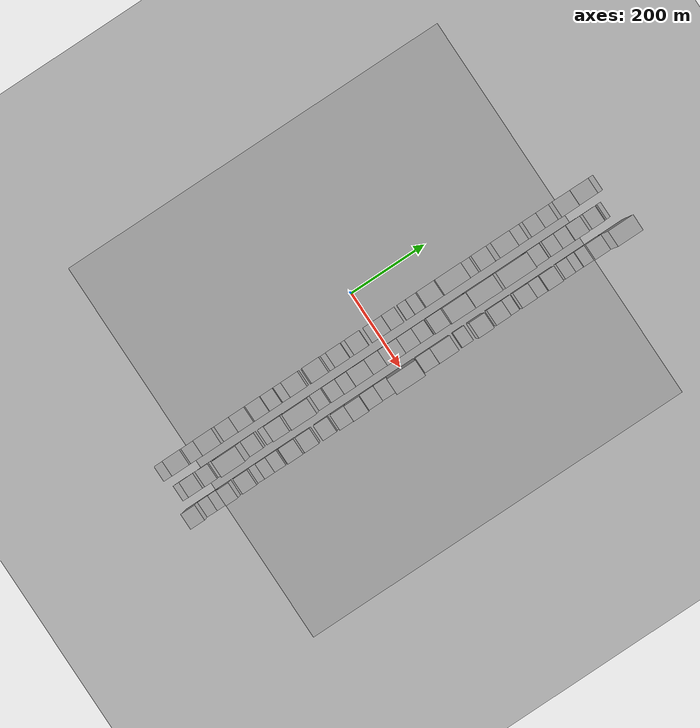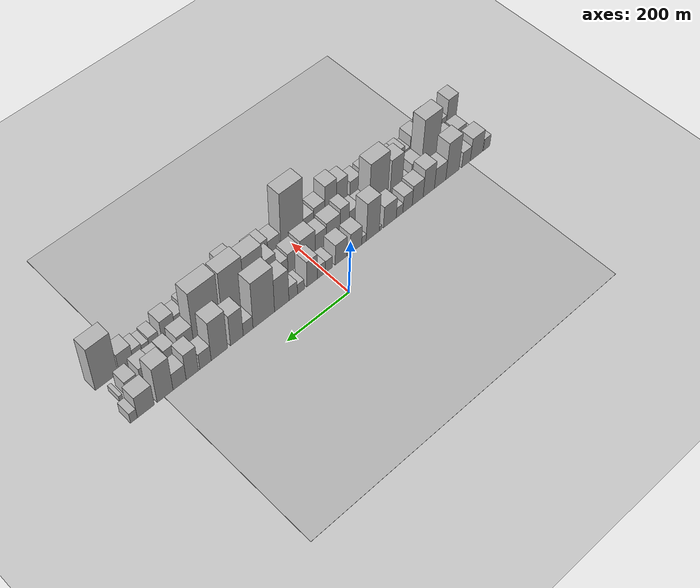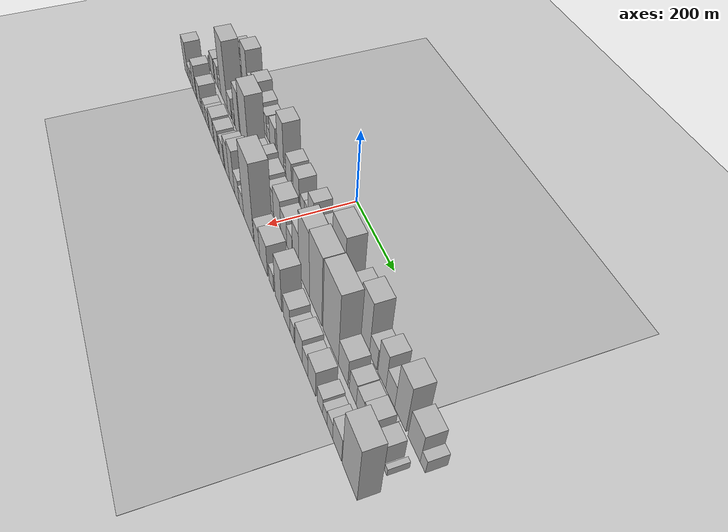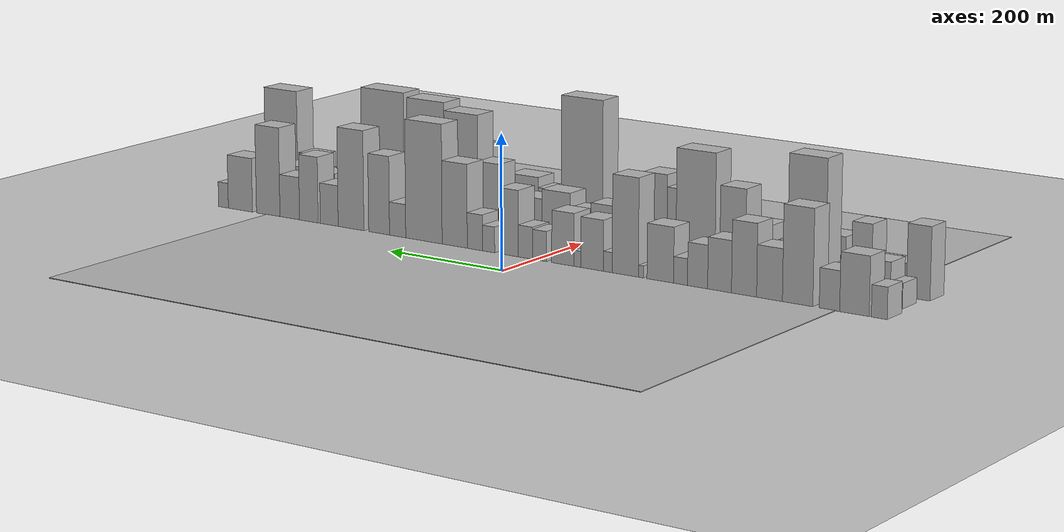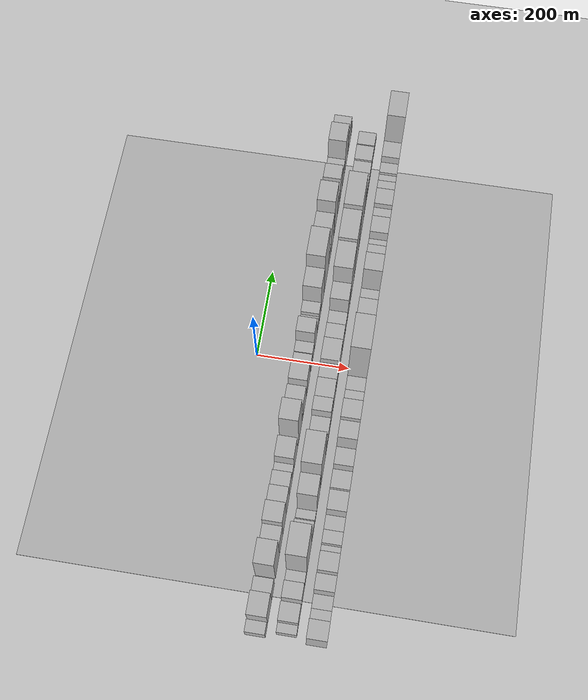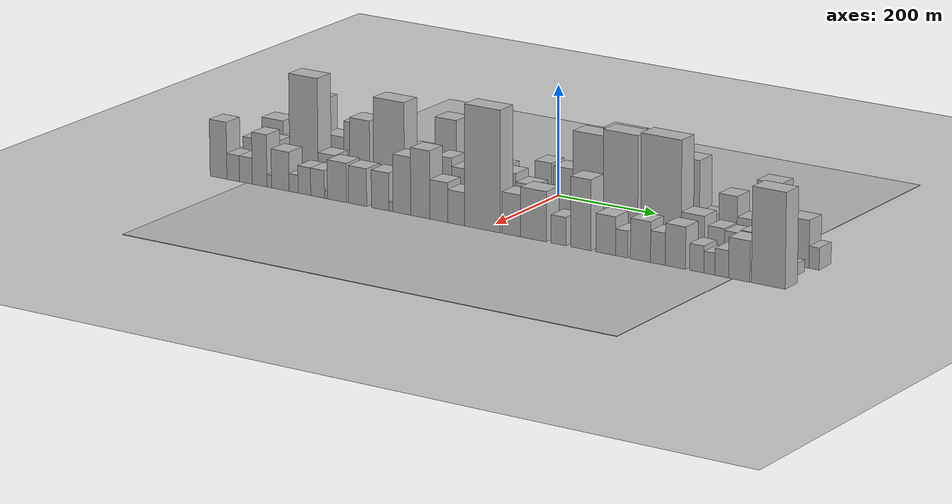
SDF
<?xml version="1.0" encoding="utf-8"?>

<sdf version="1.6">

   <world name="default">

      <gui fullscreen="0">

         <camera name="user_camera">

            <pose>-15 0 4.57585 0 0 0</pose>

            <view_controller>orbit</view_controller>

         </camera>

      </gui>

      <scene>

         <sky>

           <clouds>

             <speed>12</speed>

           </clouds>

         </sky>

         <ambient>0.4 0.4 0.4 1</ambient>

         <background>0.7 0.7 0.7 1</background>

         <shadows>1</shadows>

      </scene>

      <gravity>0 0 -9.8066</gravity>

      <magnetic_field>6e-06 2.3e-05 -4.2e-05</magnetic_field>

      <physics default="0" name="default_physics" type="ode">

         <ode>

            <solver>

               <type>quick</type>

               <iters>10</iters>

               <sor>1.0</sor>

               <use_dynamic_moi_rescaling>0</use_dynamic_moi_rescaling>

            </solver>

            <constraints>

               <cfm>0</cfm>

               <erp>0.2</erp>

               <contact_max_correcting_vel>100</contact_max_correcting_vel>

               <contact_surface_layer>0.001</contact_surface_layer>

            </constraints>

         </ode>

         <max_step_size>0.004</max_step_size>

         <real_time_factor>1</real_time_factor>

         <real_time_update_rate>250</real_time_update_rate>

      </physics>

      <light name="sun" type="directional">

         <cast_shadows>1</cast_shadows>

         <pose>0 0 10 0 0 0</pose>

         <diffuse>0.8 0.8 0.8 1</diffuse>

         <specular>0.2 0.2 0.2 1</specular>

         <attenuation>

            <range>1000</range>

            <constant>0.9</constant>

            <linear>0.01</linear>

            <quadratic>0.001</quadratic>

         </attenuation>

         <direction>-0.5 0.1 -0.9</direction>

      </light>

      <include>

         <name>ground_plane_1</name>

         <uri>model://HANNAS_ground_plane</uri>

         <pose>0 0 0  0 0 0</pose>

      </include>

      <include>

         <name>ground_plane_2</name>

         <uri>model://HANNAS_ground_plane</uri>

         <pose>100 0 0  0 0 0</pose>

      </include>

      <model name="building_1">

         <static>1</static>

         <pose frame="">100.0000 -567.7578 0 0.000000 0.000000 0.000000</pose>

         <link name="link">

            <pose frame="">0 0 22.50 0 0 0</pose>

            <collision name="collision">

               <geometry>

                  <box>

                     <size>40.0000 24.4843 45.0000</size>

                  </box>

               </geometry>

               <max_contacts>10</max_contacts>

               <surface>

                  <contact>

                     <ode/>

                  </contact>

                  <bounce/>

                  <friction>

                     <torsional>

                        <ode/>

                     </torsional>

                     <ode/>

                  </friction>

               </surface>

            </collision>

            <visual name="visual">

               <cast_shadows>0</cast_shadows>

               <geometry>

                  <box>

                     <size>40.0000 24.4843 45.0000</size>

                  </box>

               </geometry>

               <material>

                  <script>

                     <uri>model://HANNAS_wall/materials/scripts</uri>

                     <uri>model://HANNAS_wall/materials/textures</uri>

                     <name>vrc/HANNAS_wall</name>

                  </script>

               </material>

            </visual>

            <self_collide>0</self_collide>

            <enable_wind>0</enable_wind>

            <kinematic>0</kinematic>

         </link>

      </model>

      <model name="building_2">

         <static>1</static>

         <pose frame="">100.0000 -529.5423 0 0.000000 0.000000 0.000000</pose>

         <link name="link">

            <pose frame="">0 0 42.00 0 0 0</pose>

            <collision name="collision">

               <geometry>

                  <box>

                     <size>40.0000 45.9467 84.0000</size>

                  </box>

               </geometry>

               <max_contacts>10</max_contacts>

               <surface>

                  <contact>

                     <ode/>

                  </contact>

                  <bounce/>

                  <friction>

                     <torsional>

                        <ode/>

                     </torsional>

                     <ode/>

                  </friction>

               </surface>

            </collision>

            <visual name="visual">

               <cast_shadows>0</cast_shadows>

               <geometry>

                  <box>

                     <size>40.0000 45.9467 84.0000</size>

                  </box>

               </geometry>

               <material>

                  <script>

                     <uri>model://HANNAS_wall/materials/scripts</uri>

                     <uri>model://HANNAS_wall/materials/textures</uri>

                     <name>vrc/HANNAS_wall</name>

                  </script>

               </material>

            </visual>

            <self_collide>0</self_collide>

            <enable_wind>0</enable_wind>

            <kinematic>0</kinematic>

         </link>

      </model>

      <model name="building_3">

         <static>1</static>

         <pose frame="">100.0000 -490.5486 0 0.000000 0.000000 0.000000</pose>

         <link name="link">

            <pose frame="">0 0 28.50 0 0 0</pose>

            <collision name="collision">

               <geometry>

                  <box>

                     <size>40.0000 32.0408 57.0000</size>

                  </box>

               </geometry>

               <max_contacts>10</max_contacts>

               <surface>

                  <contact>

                     <ode/>

                  </contact>

                  <bounce/>

                  <friction>

                     <torsional>

                        <ode/>

                     </torsional>

                     <ode/>

                  </friction>

               </surface>

            </collision>

            <visual name="visual">

               <cast_shadows>0</cast_shadows>

               <geometry>

                  <box>

                     <size>40.0000 32.0408 57.0000</size>

                  </box>

               </geometry>

               <material>

                  <script>

                     <uri>model://HANNAS_wall/materials/scripts</uri>

                     <uri>model://HANNAS_wall/materials/textures</uri>

                     <name>vrc/HANNAS_wall</name>

                  </script>

               </material>

            </visual>

            <self_collide>0</self_collide>

            <enable_wind>0</enable_wind>

            <kinematic>0</kinematic>

         </link>

      </model>

      <model name="building_4">

         <static>1</static>

         <pose frame="">100.0000 -440.3188 0 0.000000 0.000000 0.000000</pose>

         <link name="link">

            <pose frame="">0 0 69.00 0 0 0</pose>

            <collision name="collision">

               <geometry>

                  <box>

                     <size>40.0000 48.4188 138.0000</size>

                  </box>

               </geometry>

               <max_contacts>10</max_contacts>

               <surface>

                  <contact>

                     <ode/>

                  </contact>

                  <bounce/>

                  <friction>

                     <torsional>

                        <ode/>

                     </torsional>

                     <ode/>

                  </friction>

               </surface>

            </collision>

            <visual name="visual">

               <cast_shadows>0</cast_shadows>

               <geometry>

                  <box>

                     <size>40.0000 48.4188 138.0000</size>

                  </box>

               </geometry>

               <material>

                  <script>

                     <uri>model://HANNAS_wall/materials/scripts</uri>

                     <uri>model://HANNAS_wall/materials/textures</uri>

                     <name>vrc/HANNAS_wall</name>

                  </script>

               </material>

            </visual>

            <self_collide>0</self_collide>

            <enable_wind>0</enable_wind>

            <kinematic>0</kinematic>

         </link>

      </model>

      <model name="building_5">

         <static>1</static>

         <pose frame="">100.0000 -395.4479 0 0.000000 0.000000 0.000000</pose>

         <link name="link">

            <pose frame="">0 0 37.50 0 0 0</pose>

            <collision name="collision">

               <geometry>

                  <box>

                     <size>40.0000 41.3229 75.0000</size>

                  </box>

               </geometry>

               <max_contacts>10</max_contacts>

               <surface>

                  <contact>

                     <ode/>

                  </contact>

                  <bounce/>

                  <friction>

                     <torsional>

                        <ode/>

                     </torsional>

                     <ode/>

                  </friction>

               </surface>

            </collision>

            <visual name="visual">

               <cast_shadows>0</cast_shadows>

               <geometry>

                  <box>

                     <size>40.0000 41.3229 75.0000</size>

                  </box>

               </geometry>

               <material>

                  <script>

                     <uri>model://HANNAS_wall/materials/scripts</uri>

                     <uri>model://HANNAS_wall/materials/textures</uri>

                     <name>vrc/HANNAS_wall</name>

                  </script>

               </material>

            </visual>

            <self_collide>0</self_collide>

            <enable_wind>0</enable_wind>

            <kinematic>0</kinematic>

         </link>

      </model>

      <model name="building_6">

         <static>1</static>

         <pose frame="">100.0000 -354.4409 0 0.000000 0.000000 0.000000</pose>

         <link name="link">

            <pose frame="">0 0 52.50 0 0 0</pose>

            <collision name="collision">

               <geometry>

                  <box>

                     <size>40.0000 40.6911 105.0000</size>

                  </box>

               </geometry>

               <max_contacts>10</max_contacts>

               <surface>

                  <contact>

                     <ode/>

                  </contact>

                  <bounce/>

                  <friction>

                     <torsional>

                        <ode/>

                     </torsional>

                     <ode/>

                  </friction>

               </surface>

            </collision>

            <visual name="visual">

               <cast_shadows>0</cast_shadows>

               <geometry>

                  <box>

                     <size>40.0000 40.6911 105.0000</size>

                  </box>

               </geometry>

               <material>

                  <script>

                     <uri>model://HANNAS_wall/materials/scripts</uri>

                     <uri>model://HANNAS_wall/materials/textures</uri>

                     <name>vrc/HANNAS_wall</name>

                  </script>

               </material>

            </visual>

            <self_collide>0</self_collide>

            <enable_wind>0</enable_wind>

            <kinematic>0</kinematic>

         </link>

      </model>

      <model name="building_7">

         <static>1</static>

         <pose frame="">100.0000 -314.5733 0 0.000000 0.000000 0.000000</pose>

         <link name="link">

            <pose frame="">0 0 37.50 0 0 0</pose>

            <collision name="collision">

               <geometry>

                  <box>

                     <size>40.0000 39.0440 75.0000</size>

                  </box>

               </geometry>

               <max_contacts>10</max_contacts>

               <surface>

                  <contact>

                     <ode/>

                  </contact>

                  <bounce/>

                  <friction>

                     <torsional>

                        <ode/>

                     </torsional>

                     <ode/>

                  </friction>

               </surface>

            </collision>

            <visual name="visual">

               <cast_shadows>0</cast_shadows>

               <geometry>

                  <box>

                     <size>40.0000 39.0440 75.0000</size>

                  </box>

               </geometry>

               <material>

                  <script>

                     <uri>model://HANNAS_wall/materials/scripts</uri>

                     <uri>model://HANNAS_wall/materials/textures</uri>

                     <name>vrc/HANNAS_wall</name>

                  </script>

               </material>

            </visual>

            <self_collide>0</self_collide>

            <enable_wind>0</enable_wind>

            <kinematic>0</kinematic>

         </link>

      </model>

      <model name="building_8">

         <static>1</static>

         <pose frame="">100.0000 -278.4260 0 0.000000 0.000000 0.000000</pose>

         <link name="link">

            <pose frame="">0 0 31.50 0 0 0</pose>

            <collision name="collision">

               <geometry>

                  <box>

                     <size>40.0000 33.2507 63.0000</size>

                  </box>

               </geometry>

               <max_contacts>10</max_contacts>

               <surface>

                  <contact>

                     <ode/>

                  </contact>

                  <bounce/>

                  <friction>

                     <torsional>

                        <ode/>

                     </torsional>

                     <ode/>

                  </friction>

               </surface>

            </collision>

            <visual name="visual">

               <cast_shadows>0</cast_shadows>

               <geometry>

                  <box>

                     <size>40.0000 33.2507 63.0000</size>

                  </box>

               </geometry>

               <material>

                  <script>

                     <uri>model://HANNAS_wall/materials/scripts</uri>

                     <uri>model://HANNAS_wall/materials/textures</uri>

                     <name>vrc/HANNAS_wall</name>

                  </script>

               </material>

            </visual>

            <self_collide>0</self_collide>

            <enable_wind>0</enable_wind>

            <kinematic>0</kinematic>

         </link>

      </model>

      <model name="building_9">

         <static>1</static>

         <pose frame="">100.0000 -250.2891 0 0.000000 0.000000 0.000000</pose>

         <link name="link">

            <pose frame="">0 0 19.50 0 0 0</pose>

            <collision name="collision">

               <geometry>

                  <box>

                     <size>40.0000 23.0232 39.0000</size>

                  </box>

               </geometry>

               <max_contacts>10</max_contacts>

               <surface>

                  <contact>

                     <ode/>

                  </contact>

                  <bounce/>

                  <friction>

                     <torsional>

                        <ode/>

                     </torsional>

                     <ode/>

                  </friction>

               </surface>

            </collision>

            <visual name="visual">

               <cast_shadows>0</cast_shadows>

               <geometry>

                  <box>

                     <size>40.0000 23.0232 39.0000</size>

                  </box>

               </geometry>

               <material>

                  <script>

                     <uri>model://HANNAS_wall/materials/scripts</uri>

                     <uri>model://HANNAS_wall/materials/textures</uri>

                     <name>vrc/HANNAS_wall</name>

                  </script>

               </material>

            </visual>

            <self_collide>0</self_collide>

            <enable_wind>0</enable_wind>

            <kinematic>0</kinematic>

         </link>

      </model>

      <model name="building_10">

         <static>1</static>

         <pose frame="">100.0000 -216.4399 0 0.000000 0.000000 0.000000</pose>

         <link name="link">

            <pose frame="">0 0 40.50 0 0 0</pose>

            <collision name="collision">

               <geometry>

                  <box>

                     <size>40.0000 44.6752 81.0000</size>

                  </box>

               </geometry>

               <max_contacts>10</max_contacts>

               <surface>

                  <contact>

                     <ode/>

                  </contact>

                  <bounce/>

                  <friction>

                     <torsional>

                        <ode/>

                     </torsional>

                     <ode/>

                  </friction>

               </surface>

            </collision>

            <visual name="visual">

               <cast_shadows>0</cast_shadows>

               <geometry>

                  <box>

                     <size>40.0000 44.6752 81.0000</size>

                  </box>

               </geometry>

               <material>

                  <script>

                     <uri>model://HANNAS_wall/materials/scripts</uri>

                     <uri>model://HANNAS_wall/materials/textures</uri>

                     <name>vrc/HANNAS_wall</name>

                  </script>

               </material>

            </visual>

            <self_collide>0</self_collide>

            <enable_wind>0</enable_wind>

            <kinematic>0</kinematic>

         </link>

      </model>

      <model name="building_11">

         <static>1</static>

         <pose frame="">100.0000 -183.8560 0 0.000000 0.000000 0.000000</pose>

         <link name="link">

            <pose frame="">0 0 9.00 0 0 0</pose>

            <collision name="collision">

               <geometry>

                  <box>

                     <size>40.0000 8.4927 18.0000</size>

                  </box>

               </geometry>

               <max_contacts>10</max_contacts>

               <surface>

                  <contact>

                     <ode/>

                  </contact>

                  <bounce/>

                  <friction>

                     <torsional>

                        <ode/>

                     </torsional>

                     <ode/>

                  </friction>

               </surface>

            </collision>

            <visual name="visual">

               <cast_shadows>0</cast_shadows>

               <geometry>

                  <box>

                     <size>40.0000 8.4927 18.0000</size>

                  </box>

               </geometry>

               <material>

                  <script>

                     <uri>model://HANNAS_wall/materials/scripts</uri>

                     <uri>model://HANNAS_wall/materials/textures</uri>

                     <name>vrc/HANNAS_wall</name>

                  </script>

               </material>

            </visual>

            <self_collide>0</self_collide>

            <enable_wind>0</enable_wind>

            <kinematic>0</kinematic>

         </link>

      </model>

      <model name="building_12">

         <static>1</static>

         <pose frame="">100.0000 -157.3090 0 0.000000 0.000000 0.000000</pose>

         <link name="link">

            <pose frame="">0 0 72.00 0 0 0</pose>

            <collision name="collision">

               <geometry>

                  <box>

                     <size>40.0000 44.6012 144.0000</size>

                  </box>

               </geometry>

               <max_contacts>10</max_contacts>

               <surface>

                  <contact>

                     <ode/>

                  </contact>

                  <bounce/>

                  <friction>

                     <torsional>

                        <ode/>

                     </torsional>

                     <ode/>

                  </friction>

               </surface>

            </collision>

            <visual name="visual">

               <cast_shadows>0</cast_shadows>

               <geometry>

                  <box>

                     <size>40.0000 44.6012 144.0000</size>

                  </box>

               </geometry>

               <material>

                  <script>

                     <uri>model://HANNAS_wall/materials/scripts</uri>

                     <uri>model://HANNAS_wall/materials/textures</uri>

                     <name>vrc/HANNAS_wall</name>

                  </script>

               </material>

            </visual>

            <self_collide>0</self_collide>

            <enable_wind>0</enable_wind>

            <kinematic>0</kinematic>

         </link>

      </model>

      <model name="building_13">

         <static>1</static>

         <pose frame="">100.0000 -127.4432 0 0.000000 0.000000 0.000000</pose>

         <link name="link">

            <pose frame="">0 0 15.00 0 0 0</pose>

            <collision name="collision">

               <geometry>

                  <box>

                     <size>40.0000 15.1304 30.0000</size>

                  </box>

               </geometry>

               <max_contacts>10</max_contacts>

               <surface>

                  <contact>

                     <ode/>

                  </contact>

                  <bounce/>

                  <friction>

                     <torsional>

                        <ode/>

                     </torsional>

                     <ode/>

                  </friction>

               </surface>

            </collision>

            <visual name="visual">

               <cast_shadows>0</cast_shadows>

               <geometry>

                  <box>

                     <size>40.0000 15.1304 30.0000</size>

                  </box>

               </geometry>

               <material>

                  <script>

                     <uri>model://HANNAS_wall/materials/scripts</uri>

                     <uri>model://HANNAS_wall/materials/textures</uri>

                     <name>vrc/HANNAS_wall</name>

                  </script>

               </material>

            </visual>

            <self_collide>0</self_collide>

            <enable_wind>0</enable_wind>

            <kinematic>0</kinematic>

         </link>

      </model>

      <model name="building_14">

         <static>1</static>

         <pose frame="">100.0000 -100.4340 0 0.000000 0.000000 0.000000</pose>

         <link name="link">

            <pose frame="">0 0 37.50 0 0 0</pose>

            <collision name="collision">

               <geometry>

                  <box>

                     <size>40.0000 38.8878 75.0000</size>

                  </box>

               </geometry>

               <max_contacts>10</max_contacts>

               <surface>

                  <contact>

                     <ode/>

                  </contact>

                  <bounce/>

                  <friction>

                     <torsional>

                        <ode/>

                     </torsional>

                     <ode/>

                  </friction>

               </surface>

            </collision>

            <visual name="visual">

               <cast_shadows>0</cast_shadows>

               <geometry>

                  <box>

                     <size>40.0000 38.8878 75.0000</size>

                  </box>

               </geometry>

               <material>

                  <script>

                     <uri>model://HANNAS_wall/materials/scripts</uri>

                     <uri>model://HANNAS_wall/materials/textures</uri>

                     <name>vrc/HANNAS_wall</name>

                  </script>

               </material>

            </visual>

            <self_collide>0</self_collide>

            <enable_wind>0</enable_wind>

            <kinematic>0</kinematic>

         </link>

      </model>

      <model name="building_15">

         <static>1</static>

         <pose frame="">100.0000 -75.2105 0 0.000000 0.000000 0.000000</pose>

         <link name="link">

            <pose frame="">0 0 12.00 0 0 0</pose>

            <collision name="collision">

               <geometry>

                  <box>

                     <size>40.0000 11.5592 24.0000</size>

                  </box>

               </geometry>

               <max_contacts>10</max_contacts>

               <surface>

                  <contact>

                     <ode/>

                  </contact>

                  <bounce/>

                  <friction>

                     <torsional>

                        <ode/>

                     </torsional>

                     <ode/>

                  </friction>

               </surface>

            </collision>

            <visual name="visual">

               <cast_shadows>0</cast_shadows>

               <geometry>

                  <box>

                     <size>40.0000 11.5592 24.0000</size>

                  </box>

               </geometry>

               <material>

                  <script>

                     <uri>model://HANNAS_wall/materials/scripts</uri>

                     <uri>model://HANNAS_wall/materials/textures</uri>

                     <name>vrc/HANNAS_wall</name>

                  </script>

               </material>

            </visual>

            <self_collide>0</self_collide>

            <enable_wind>0</enable_wind>

            <kinematic>0</kinematic>

         </link>

      </model>

      <model name="building_16">

         <static>1</static>

         <pose frame="">100.0000 -49.8729 0 0.000000 0.000000 0.000000</pose>

         <link name="link">

            <pose frame="">0 0 39.00 0 0 0</pose>

            <collision name="collision">

               <geometry>

                  <box>

                     <size>40.0000 39.1161 78.0000</size>

                  </box>

               </geometry>

               <max_contacts>10</max_contacts>

               <surface>

                  <contact>

                     <ode/>

                  </contact>

                  <bounce/>

                  <friction>

                     <torsional>

                        <ode/>

                     </torsional>

                     <ode/>

                  </friction>

               </surface>

            </collision>

            <visual name="visual">

               <cast_shadows>0</cast_shadows>

               <geometry>

                  <box>

                     <size>40.0000 39.1161 78.0000</size>

                  </box>

               </geometry>

               <material>

                  <script>

                     <uri>model://HANNAS_wall/materials/scripts</uri>

                     <uri>model://HANNAS_wall/materials/textures</uri>

                     <name>vrc/HANNAS_wall</name>

                  </script>

               </material>

            </visual>

            <self_collide>0</self_collide>

            <enable_wind>0</enable_wind>

            <kinematic>0</kinematic>

         </link>

      </model>

      <model name="building_17">

         <static>1</static>

         <pose frame="">100.0000 -9.2193 0 0.000000 0.000000 0.000000</pose>

         <link name="link">

            <pose frame="">0 0 22.50 0 0 0</pose>

            <collision name="collision">

               <geometry>

                  <box>

                     <size>40.0000 24.1911 45.0000</size>

                  </box>

               </geometry>

               <max_contacts>10</max_contacts>

               <surface>

                  <contact>

                     <ode/>

                  </contact>

                  <bounce/>

                  <friction>

                     <torsional>

                        <ode/>

                     </torsional>

                     <ode/>

                  </friction>

               </surface>

            </collision>

            <visual name="visual">

               <cast_shadows>0</cast_shadows>

               <geometry>

                  <box>

                     <size>40.0000 24.1911 45.0000</size>

                  </box>

               </geometry>

               <material>

                  <script>

                     <uri>model://HANNAS_wall/materials/scripts</uri>

                     <uri>model://HANNAS_wall/materials/textures</uri>

                     <name>vrc/HANNAS_wall</name>

                  </script>

               </material>

            </visual>

            <self_collide>0</self_collide>

            <enable_wind>0</enable_wind>

            <kinematic>0</kinematic>

         </link>

      </model>

      <model name="building_18">

         <static>1</static>

         <pose frame="">100.0000 15.7469 0 0.000000 0.000000 0.000000</pose>

         <link name="link">

            <pose frame="">0 0 24.00 0 0 0</pose>

            <collision name="collision">

               <geometry>

                  <box>

                     <size>40.0000 25.7412 48.0000</size>

                  </box>

               </geometry>

               <max_contacts>10</max_contacts>

               <surface>

                  <contact>

                     <ode/>

                  </contact>

                  <bounce/>

                  <friction>

                     <torsional>

                        <ode/>

                     </torsional>

                     <ode/>

                  </friction>

               </surface>

            </collision>

            <visual name="visual">

               <cast_shadows>0</cast_shadows>

               <geometry>

                  <box>

                     <size>40.0000 25.7412 48.0000</size>

                  </box>

               </geometry>

               <material>

                  <script>

                     <uri>model://HANNAS_wall/materials/scripts</uri>

                     <uri>model://HANNAS_wall/materials/textures</uri>

                     <name>vrc/HANNAS_wall</name>

                  </script>

               </material>

            </visual>

            <self_collide>0</self_collide>

            <enable_wind>0</enable_wind>

            <kinematic>0</kinematic>

         </link>

      </model>

      <model name="building_19">

         <static>1</static>

         <pose frame="">100.0000 45.7163 0 0.000000 0.000000 0.000000</pose>

         <link name="link">

            <pose frame="">0 0 49.50 0 0 0</pose>

            <collision name="collision">

               <geometry>

                  <box>

                     <size>40.0000 34.1975 99.0000</size>

                  </box>

               </geometry>

               <max_contacts>10</max_contacts>

               <surface>

                  <contact>

                     <ode/>

                  </contact>

                  <bounce/>

                  <friction>

                     <torsional>

                        <ode/>

                     </torsional>

                     <ode/>

                  </friction>

               </surface>

            </collision>

            <visual name="visual">

               <cast_shadows>0</cast_shadows>

               <geometry>

                  <box>

                     <size>40.0000 34.1975 99.0000</size>

                  </box>

               </geometry>

               <material>

                  <script>

                     <uri>model://HANNAS_wall/materials/scripts</uri>

                     <uri>model://HANNAS_wall/materials/textures</uri>

                     <name>vrc/HANNAS_wall</name>

                  </script>

               </material>

            </visual>

            <self_collide>0</self_collide>

            <enable_wind>0</enable_wind>

            <kinematic>0</kinematic>

         </link>

      </model>

      <model name="building_20">

         <static>1</static>

         <pose frame="">100.0000 81.9478 0 0.000000 0.000000 0.000000</pose>

         <link name="link">

            <pose frame="">0 0 19.50 0 0 0</pose>

            <collision name="collision">

               <geometry>

                  <box>

                     <size>40.0000 22.2656 39.0000</size>

                  </box>

               </geometry>

               <max_contacts>10</max_contacts>

               <surface>

                  <contact>

                     <ode/>

                  </contact>

                  <bounce/>

                  <friction>

                     <torsional>

                        <ode/>

                     </torsional>

                     <ode/>

                  </friction>

               </surface>

            </collision>

            <visual name="visual">

               <cast_shadows>0</cast_shadows>

               <geometry>

                  <box>

                     <size>40.0000 22.2656 39.0000</size>

                  </box>

               </geometry>

               <material>

                  <script>

                     <uri>model://HANNAS_wall/materials/scripts</uri>

                     <uri>model://HANNAS_wall/materials/textures</uri>

                     <name>vrc/HANNAS_wall</name>

                  </script>

               </material>

            </visual>

            <self_collide>0</self_collide>

            <enable_wind>0</enable_wind>

            <kinematic>0</kinematic>

         </link>

      </model>

      <model name="building_21">

         <static>1</static>

         <pose frame="">100.0000 106.7614 0 0.000000 0.000000 0.000000</pose>

         <link name="link">

            <pose frame="">0 0 27.00 0 0 0</pose>

            <collision name="collision">

               <geometry>

                  <box>

                     <size>40.0000 27.3615 54.0000</size>

                  </box>

               </geometry>

               <max_contacts>10</max_contacts>

               <surface>

                  <contact>

                     <ode/>

                  </contact>

                  <bounce/>

                  <friction>

                     <torsional>

                        <ode/>

                     </torsional>

                     <ode/>

                  </friction>

               </surface>

            </collision>

            <visual name="visual">

               <cast_shadows>0</cast_shadows>

               <geometry>

                  <box>

                     <size>40.0000 27.3615 54.0000</size>

                  </box>

               </geometry>

               <material>

                  <script>

                     <uri>model://HANNAS_wall/materials/scripts</uri>

                     <uri>model://HANNAS_wall/materials/textures</uri>

                     <name>vrc/HANNAS_wall</name>

                  </script>

               </material>

            </visual>

            <self_collide>0</self_collide>

            <enable_wind>0</enable_wind>

            <kinematic>0</kinematic>

         </link>

      </model>

      <model name="building_22">

         <static>1</static>

         <pose frame="">100.0000 143.3555 0 0.000000 0.000000 0.000000</pose>

         <link name="link">

            <pose frame="">0 0 63.00 0 0 0</pose>

            <collision name="collision">

               <geometry>

                  <box>

                     <size>40.0000 45.8266 126.0000</size>

                  </box>

               </geometry>

               <max_contacts>10</max_contacts>

               <surface>

                  <contact>

                     <ode/>

                  </contact>

                  <bounce/>

                  <friction>

                     <torsional>

                        <ode/>

                     </torsional>

                     <ode/>

                  </friction>

               </surface>

            </collision>

            <visual name="visual">

               <cast_shadows>0</cast_shadows>

               <geometry>

                  <box>

                     <size>40.0000 45.8266 126.0000</size>

                  </box>

               </geometry>

               <material>

                  <script>

                     <uri>model://HANNAS_wall/materials/scripts</uri>

                     <uri>model://HANNAS_wall/materials/textures</uri>

                     <name>vrc/HANNAS_wall</name>

                  </script>

               </material>

            </visual>

            <self_collide>0</self_collide>

            <enable_wind>0</enable_wind>

            <kinematic>0</kinematic>

         </link>

      </model>

      <model name="building_23">

         <static>1</static>

         <pose frame="">100.0000 199.9221 0 0.000000 0.000000 0.000000</pose>

         <link name="link">

            <pose frame="">0 0 90.00 0 0 0</pose>

            <collision name="collision">

               <geometry>

                  <box>

                     <size>40.0000 67.3065 180.0000</size>

                  </box>

               </geometry>

               <max_contacts>10</max_contacts>

               <surface>

                  <contact>

                     <ode/>

                  </contact>

                  <bounce/>

                  <friction>

                     <torsional>

                        <ode/>

                     </torsional>

                     <ode/>

                  </friction>

               </surface>

            </collision>

            <visual name="visual">

               <cast_shadows>0</cast_shadows>

               <geometry>

                  <box>

                     <size>40.0000 67.3065 180.0000</size>

                  </box>

               </geometry>

               <material>

                  <script>

                     <uri>model://HANNAS_wall/materials/scripts</uri>

                     <uri>model://HANNAS_wall/materials/textures</uri>

                     <name>vrc/HANNAS_wall</name>

                  </script>

               </material>

            </visual>

            <self_collide>0</self_collide>

            <enable_wind>0</enable_wind>

            <kinematic>0</kinematic>

         </link>

      </model>

      <model name="building_24">

         <static>1</static>

         <pose frame="">100.0000 248.7436 0 0.000000 0.000000 0.000000</pose>

         <link name="link">

            <pose frame="">0 0 25.50 0 0 0</pose>

            <collision name="collision">

               <geometry>

                  <box>

                     <size>40.0000 30.3366 51.0000</size>

                  </box>

               </geometry>

               <max_contacts>10</max_contacts>

               <surface>

                  <contact>

                     <ode/>

                  </contact>

                  <bounce/>

                  <friction>

                     <torsional>

                        <ode/>

                     </torsional>

                     <ode/>

                  </friction>

               </surface>

            </collision>

            <visual name="visual">

               <cast_shadows>0</cast_shadows>

               <geometry>

                  <box>

                     <size>40.0000 30.3366 51.0000</size>

                  </box>

               </geometry>

               <material>

                  <script>

                     <uri>model://HANNAS_wall/materials/scripts</uri>

                     <uri>model://HANNAS_wall/materials/textures</uri>

                     <name>vrc/HANNAS_wall</name>

                  </script>

               </material>

            </visual>

            <self_collide>0</self_collide>

            <enable_wind>0</enable_wind>

            <kinematic>0</kinematic>

         </link>

      </model>

      <model name="building_25">

         <static>1</static>

         <pose frame="">100.0000 283.5443 0 0.000000 0.000000 0.000000</pose>

         <link name="link">

            <pose frame="">0 0 60.00 0 0 0</pose>

            <collision name="collision">

               <geometry>

                  <box>

                     <size>40.0000 39.2648 120.0000</size>

                  </box>

               </geometry>

               <max_contacts>10</max_contacts>

               <surface>

                  <contact>

                     <ode/>

                  </contact>

                  <bounce/>

                  <friction>

                     <torsional>

                        <ode/>

                     </torsional>

                     <ode/>

                  </friction>

               </surface>

            </collision>

            <visual name="visual">

               <cast_shadows>0</cast_shadows>

               <geometry>

                  <box>

                     <size>40.0000 39.2648 120.0000</size>

                  </box>

               </geometry>

               <material>

                  <script>

                     <uri>model://HANNAS_wall/materials/scripts</uri>

                     <uri>model://HANNAS_wall/materials/textures</uri>

                     <name>vrc/HANNAS_wall</name>

                  </script>

               </material>

            </visual>

            <self_collide>0</self_collide>

            <enable_wind>0</enable_wind>

            <kinematic>0</kinematic>

         </link>

      </model>

      <model name="building_26">

         <static>1</static>

         <pose frame="">100.0000 336.8091 0 0.000000 0.000000 0.000000</pose>

         <link name="link">

            <pose frame="">0 0 76.50 0 0 0</pose>

            <collision name="collision">

               <geometry>

                  <box>

                     <size>40.0000 49.2648 153.0000</size>

                  </box>

               </geometry>

               <max_contacts>10</max_contacts>

               <surface>

                  <contact>

                     <ode/>

                  </contact>

                  <bounce/>

                  <friction>

                     <torsional>

                        <ode/>

                     </torsional>

                     <ode/>

                  </friction>

               </surface>

            </collision>

            <visual name="visual">

               <cast_shadows>0</cast_shadows>

               <geometry>

                  <box>

                     <size>40.0000 49.2648 153.0000</size>

                  </box>

               </geometry>

               <material>

                  <script>

                     <uri>model://HANNAS_wall/materials/scripts</uri>

                     <uri>model://HANNAS_wall/materials/textures</uri>

                     <name>vrc/HANNAS_wall</name>

                  </script>

               </material>

            </visual>

            <self_collide>0</self_collide>

            <enable_wind>0</enable_wind>

            <kinematic>0</kinematic>

         </link>

      </model>

      <model name="building_27">

         <static>1</static>

         <pose frame="">100.0000 378.6815 0 0.000000 0.000000 0.000000</pose>

         <link name="link">

            <pose frame="">0 0 31.50 0 0 0</pose>

            <collision name="collision">

               <geometry>

                  <box>

                     <size>40.0000 34.4800 63.0000</size>

                  </box>

               </geometry>

               <max_contacts>10</max_contacts>

               <surface>

                  <contact>

                     <ode/>

                  </contact>

                  <bounce/>

                  <friction>

                     <torsional>

                        <ode/>

                     </torsional>

                     <ode/>

                  </friction>

               </surface>

            </collision>

            <visual name="visual">

               <cast_shadows>0</cast_shadows>

               <geometry>

                  <box>

                     <size>40.0000 34.4800 63.0000</size>

                  </box>

               </geometry>

               <material>

                  <script>

                     <uri>model://HANNAS_wall/materials/scripts</uri>

                     <uri>model://HANNAS_wall/materials/textures</uri>

                     <name>vrc/HANNAS_wall</name>

                  </script>

               </material>

            </visual>

            <self_collide>0</self_collide>

            <enable_wind>0</enable_wind>

            <kinematic>0</kinematic>

         </link>

      </model>

      <model name="building_28">

         <static>1</static>

         <pose frame="">100.0000 417.9894 0 0.000000 0.000000 0.000000</pose>

         <link name="link">

            <pose frame="">0 0 51.00 0 0 0</pose>

            <collision name="collision">

               <geometry>

                  <box>

                     <size>40.0000 36.1358 102.0000</size>

                  </box>

               </geometry>

               <max_contacts>10</max_contacts>

               <surface>

                  <contact>

                     <ode/>

                  </contact>

                  <bounce/>

                  <friction>

                     <torsional>

                        <ode/>

                     </torsional>

                     <ode/>

                  </friction>

               </surface>

            </collision>

            <visual name="visual">

               <cast_shadows>0</cast_shadows>

               <geometry>

                  <box>

                     <size>40.0000 36.1358 102.0000</size>

                  </box>

               </geometry>

               <material>

                  <script>

                     <uri>model://HANNAS_wall/materials/scripts</uri>

                     <uri>model://HANNAS_wall/materials/textures</uri>

                     <name>vrc/HANNAS_wall</name>

                  </script>

               </material>

            </visual>

            <self_collide>0</self_collide>

            <enable_wind>0</enable_wind>

            <kinematic>0</kinematic>

         </link>

      </model>

      <model name="building_29">

         <static>1</static>

         <pose frame="">100.0000 455.2565 0 0.000000 0.000000 0.000000</pose>

         <link name="link">

            <pose frame="">0 0 33.00 0 0 0</pose>

            <collision name="collision">

               <geometry>

                  <box>

                     <size>40.0000 38.3985 66.0000</size>

                  </box>

               </geometry>

               <max_contacts>10</max_contacts>

               <surface>

                  <contact>

                     <ode/>

                  </contact>

                  <bounce/>

                  <friction>

                     <torsional>

                        <ode/>

                     </torsional>

                     <ode/>

                  </friction>

               </surface>

            </collision>

            <visual name="visual">

               <cast_shadows>0</cast_shadows>

               <geometry>

                  <box>

                     <size>40.0000 38.3985 66.0000</size>

                  </box>

               </geometry>

               <material>

                  <script>

                     <uri>model://HANNAS_wall/materials/scripts</uri>

                     <uri>model://HANNAS_wall/materials/textures</uri>

                     <name>vrc/HANNAS_wall</name>

                  </script>

               </material>

            </visual>

            <self_collide>0</self_collide>

            <enable_wind>0</enable_wind>

            <kinematic>0</kinematic>

         </link>

      </model>

      <model name="building_30">

         <static>1</static>

         <pose frame="">100.0000 497.6974 0 0.000000 0.000000 0.000000</pose>

         <link name="link">

            <pose frame="">0 0 69.00 0 0 0</pose>

            <collision name="collision">

               <geometry>

                  <box>

                     <size>40.0000 46.4833 138.0000</size>

                  </box>

               </geometry>

               <max_contacts>10</max_contacts>

               <surface>

                  <contact>

                     <ode/>

                  </contact>

                  <bounce/>

                  <friction>

                     <torsional>

                        <ode/>

                     </torsional>

                     <ode/>

                  </friction>

               </surface>

            </collision>

            <visual name="visual">

               <cast_shadows>0</cast_shadows>

               <geometry>

                  <box>

                     <size>40.0000 46.4833 138.0000</size>

                  </box>

               </geometry>

               <material>

                  <script>

                     <uri>model://HANNAS_wall/materials/scripts</uri>

                     <uri>model://HANNAS_wall/materials/textures</uri>

                     <name>vrc/HANNAS_wall</name>

                  </script>

               </material>

            </visual>

            <self_collide>0</self_collide>

            <enable_wind>0</enable_wind>

            <kinematic>0</kinematic>

         </link>

      </model>

      <model name="building_31">

         <static>1</static>

         <pose frame="">100.0000 553.1227 0 0.000000 0.000000 0.000000</pose>

         <link name="link">

            <pose frame="">0 0 42.00 0 0 0</pose>

            <collision name="collision">

               <geometry>

                  <box>

                     <size>40.0000 48.3673 84.0000</size>

                  </box>

               </geometry>

               <max_contacts>10</max_contacts>

               <surface>

                  <contact>

                     <ode/>

                  </contact>

                  <bounce/>

                  <friction>

                     <torsional>

                        <ode/>

                     </torsional>

                     <ode/>

                  </friction>

               </surface>

            </collision>

            <visual name="visual">

               <cast_shadows>0</cast_shadows>

               <geometry>

                  <box>

                     <size>40.0000 48.3673 84.0000</size>

                  </box>

               </geometry>

               <material>

                  <script>

                     <uri>model://HANNAS_wall/materials/scripts</uri>

                     <uri>model://HANNAS_wall/materials/textures</uri>

                     <name>vrc/HANNAS_wall</name>

                  </script>

               </material>

            </visual>

            <self_collide>0</self_collide>

            <enable_wind>0</enable_wind>

            <kinematic>0</kinematic>

         </link>

      </model>

      <model name="building_32">

         <static>1</static>

         <pose frame="">100.0000 587.1421 0 0.000000 0.000000 0.000000</pose>

         <link name="link">

            <pose frame="">0 0 19.50 0 0 0</pose>

            <collision name="collision">

               <geometry>

                  <box>

                     <size>40.0000 19.6715 39.0000</size>

                  </box>

               </geometry>

               <max_contacts>10</max_contacts>

               <surface>

                  <contact>

                     <ode/>

                  </contact>

                  <bounce/>

                  <friction>

                     <torsional>

                        <ode/>

                     </torsional>

                     <ode/>

                  </friction>

               </surface>

            </collision>

            <visual name="visual">

               <cast_shadows>0</cast_shadows>

               <geometry>

                  <box>

                     <size>40.0000 19.6715 39.0000</size>

                  </box>

               </geometry>

               <material>

                  <script>

                     <uri>model://HANNAS_wall/materials/scripts</uri>

                     <uri>model://HANNAS_wall/materials/textures</uri>

                     <name>vrc/HANNAS_wall</name>

                  </script>

               </material>

            </visual>

            <self_collide>0</self_collide>

            <enable_wind>0</enable_wind>

            <kinematic>0</kinematic>

         </link>

      </model>

      <model name="building_33">

         <static>1</static>

         <pose frame="">160.0000 -560.4927 0 0.000000 0.000000 0.000000</pose>

         <link name="link">

            <pose frame="">0 0 18.00 0 0 0</pose>

            <collision name="collision">

               <geometry>

                  <box>

                     <size>40.0000 19.0145 36.0000</size>

                  </box>

               </geometry>

               <max_contacts>10</max_contacts>

               <surface>

                  <contact>

                     <ode/>

                  </contact>

                  <bounce/>

                  <friction>

                     <torsional>

                        <ode/>

                     </torsional>

                     <ode/>

                  </friction>

               </surface>

            </collision>

            <visual name="visual">

               <cast_shadows>0</cast_shadows>

               <geometry>

                  <box>

                     <size>40.0000 19.0145 36.0000</size>

                  </box>

               </geometry>

               <material>

                  <script>

                     <uri>model://HANNAS_wall/materials/scripts</uri>

                     <uri>model://HANNAS_wall/materials/textures</uri>

                     <name>vrc/HANNAS_wall</name>

                  </script>

               </material>

            </visual>

            <self_collide>0</self_collide>

            <enable_wind>0</enable_wind>

            <kinematic>0</kinematic>

         </link>

      </model>

      <model name="building_34">

         <static>1</static>

         <pose frame="">160.0000 -532.4048 0 0.000000 0.000000 0.000000</pose>

         <link name="link">

            <pose frame="">0 0 31.50 0 0 0</pose>

            <collision name="collision">

               <geometry>

                  <box>

                     <size>40.0000 37.1614 63.0000</size>

                  </box>

               </geometry>

               <max_contacts>10</max_contacts>

               <surface>

                  <contact>

                     <ode/>

                  </contact>

                  <bounce/>

                  <friction>

                     <torsional>

                        <ode/>

                     </torsional>

                     <ode/>

                  </friction>

               </surface>

            </collision>

            <visual name="visual">

               <cast_shadows>0</cast_shadows>

               <geometry>

                  <box>

                     <size>40.0000 37.1614 63.0000</size>

                  </box>

               </geometry>

               <material>

                  <script>

                     <uri>model://HANNAS_wall/materials/scripts</uri>

                     <uri>model://HANNAS_wall/materials/textures</uri>

                     <name>vrc/HANNAS_wall</name>

                  </script>

               </material>

            </visual>

            <self_collide>0</self_collide>

            <enable_wind>0</enable_wind>

            <kinematic>0</kinematic>

         </link>

      </model>

      <model name="building_35">

         <static>1</static>

         <pose frame="">160.0000 -491.1633 0 0.000000 0.000000 0.000000</pose>

         <link name="link">

            <pose frame="">0 0 33.00 0 0 0</pose>

            <collision name="collision">

               <geometry>

                  <box>

                     <size>40.0000 33.3217 66.0000</size>

                  </box>

               </geometry>

               <max_contacts>10</max_contacts>

               <surface>

                  <contact>

                     <ode/>

                  </contact>

                  <bounce/>

                  <friction>

                     <torsional>

                        <ode/>

                     </torsional>

                     <ode/>

                  </friction>

               </surface>

            </collision>

            <visual name="visual">

               <cast_shadows>0</cast_shadows>

               <geometry>

                  <box>

                     <size>40.0000 33.3217 66.0000</size>

                  </box>

               </geometry>

               <material>

                  <script>

                     <uri>model://HANNAS_wall/materials/scripts</uri>

                     <uri>model://HANNAS_wall/materials/textures</uri>

                     <name>vrc/HANNAS_wall</name>

                  </script>

               </material>

            </visual>

            <self_collide>0</self_collide>

            <enable_wind>0</enable_wind>

            <kinematic>0</kinematic>

         </link>

      </model>

      <model name="building_36">

         <static>1</static>

         <pose frame="">160.0000 -461.9633 0 0.000000 0.000000 0.000000</pose>

         <link name="link">

            <pose frame="">0 0 21.00 0 0 0</pose>

            <collision name="collision">

               <geometry>

                  <box>

                     <size>40.0000 25.0782 42.0000</size>

                  </box>

               </geometry>

               <max_contacts>10</max_contacts>

               <surface>

                  <contact>

                     <ode/>

                  </contact>

                  <bounce/>

                  <friction>

                     <torsional>

                        <ode/>

                     </torsional>

                     <ode/>

                  </friction>

               </surface>

            </collision>

            <visual name="visual">

               <cast_shadows>0</cast_shadows>

               <geometry>

                  <box>

                     <size>40.0000 25.0782 42.0000</size>

                  </box>

               </geometry>

               <material>

                  <script>

                     <uri>model://HANNAS_wall/materials/scripts</uri>

                     <uri>model://HANNAS_wall/materials/textures</uri>

                     <name>vrc/HANNAS_wall</name>

                  </script>

               </material>

            </visual>

            <self_collide>0</self_collide>

            <enable_wind>0</enable_wind>

            <kinematic>0</kinematic>

         </link>

      </model>

      <model name="building_37">

         <static>1</static>

         <pose frame="">160.0000 -418.6511 0 0.000000 0.000000 0.000000</pose>

         <link name="link">

            <pose frame="">0 0 97.50 0 0 0</pose>

            <collision name="collision">

               <geometry>

                  <box>

                     <size>40.0000 61.5463 195.0000</size>

                  </box>

               </geometry>

               <max_contacts>10</max_contacts>

               <surface>

                  <contact>

                     <ode/>

                  </contact>

                  <bounce/>

                  <friction>

                     <torsional>

                        <ode/>

                     </torsional>

                     <ode/>

                  </friction>

               </surface>

            </collision>

            <visual name="visual">

               <cast_shadows>0</cast_shadows>

               <geometry>

                  <box>

                     <size>40.0000 61.5463 195.0000</size>

                  </box>

               </geometry>

               <material>

                  <script>

                     <uri>model://HANNAS_wall/materials/scripts</uri>

                     <uri>model://HANNAS_wall/materials/textures</uri>

                     <name>vrc/HANNAS_wall</name>

                  </script>

               </material>

            </visual>

            <self_collide>0</self_collide>

            <enable_wind>0</enable_wind>

            <kinematic>0</kinematic>

         </link>

      </model>

      <model name="building_38">

         <static>1</static>

         <pose frame="">160.0000 -369.9380 0 0.000000 0.000000 0.000000</pose>

         <link name="link">

            <pose frame="">0 0 30.00 0 0 0</pose>

            <collision name="collision">

               <geometry>

                  <box>

                     <size>40.0000 35.8798 60.0000</size>

                  </box>

               </geometry>

               <max_contacts>10</max_contacts>

               <surface>

                  <contact>

                     <ode/>

                  </contact>

                  <bounce/>

                  <friction>

                     <torsional>

                        <ode/>

                     </torsional>

                     <ode/>

                  </friction>

               </surface>

            </collision>

            <visual name="visual">

               <cast_shadows>0</cast_shadows>

               <geometry>

                  <box>

                     <size>40.0000 35.8798 60.0000</size>

                  </box>

               </geometry>

               <material>

                  <script>

                     <uri>model://HANNAS_wall/materials/scripts</uri>

                     <uri>model://HANNAS_wall/materials/textures</uri>

                     <name>vrc/HANNAS_wall</name>

                  </script>

               </material>

            </visual>

            <self_collide>0</self_collide>

            <enable_wind>0</enable_wind>

            <kinematic>0</kinematic>

         </link>

      </model>

      <model name="building_39">

         <static>1</static>

         <pose frame="">160.0000 -334.4406 0 0.000000 0.000000 0.000000</pose>

         <link name="link">

            <pose frame="">0 0 16.50 0 0 0</pose>

            <collision name="collision">

               <geometry>

                  <box>

                     <size>40.0000 19.1148 33.0000</size>

                  </box>

               </geometry>

               <max_contacts>10</max_contacts>

               <surface>

                  <contact>

                     <ode/>

                  </contact>

                  <bounce/>

                  <friction>

                     <torsional>

                        <ode/>

                     </torsional>

                     <ode/>

                  </friction>

               </surface>

            </collision>

            <visual name="visual">

               <cast_shadows>0</cast_shadows>

               <geometry>

                  <box>

                     <size>40.0000 19.1148 33.0000</size>

                  </box>

               </geometry>

               <material>

                  <script>

                     <uri>model://HANNAS_wall/materials/scripts</uri>

                     <uri>model://HANNAS_wall/materials/textures</uri>

                     <name>vrc/HANNAS_wall</name>

                  </script>

               </material>

            </visual>

            <self_collide>0</self_collide>

            <enable_wind>0</enable_wind>

            <kinematic>0</kinematic>

         </link>

      </model>

      <model name="building_40">

         <static>1</static>

         <pose frame="">160.0000 -298.5327 0 0.000000 0.000000 0.000000</pose>

         <link name="link">

            <pose frame="">0 0 67.50 0 0 0</pose>

            <collision name="collision">

               <geometry>

                  <box>

                     <size>40.0000 42.7010 135.0000</size>

                  </box>

               </geometry>

               <max_contacts>10</max_contacts>

               <surface>

                  <contact>

                     <ode/>

                  </contact>

                  <bounce/>

                  <friction>

                     <torsional>

                        <ode/>

                     </torsional>

                     <ode/>

                  </friction>

               </surface>

            </collision>

            <visual name="visual">

               <cast_shadows>0</cast_shadows>

               <geometry>

                  <box>

                     <size>40.0000 42.7010 135.0000</size>

                  </box>

               </geometry>

               <material>

                  <script>

                     <uri>model://HANNAS_wall/materials/scripts</uri>

                     <uri>model://HANNAS_wall/materials/textures</uri>

                     <name>vrc/HANNAS_wall</name>

                  </script>

               </material>

            </visual>

            <self_collide>0</self_collide>

            <enable_wind>0</enable_wind>

            <kinematic>0</kinematic>

         </link>

      </model>

      <model name="building_41">

         <static>1</static>

         <pose frame="">160.0000 -236.5103 0 0.000000 0.000000 0.000000</pose>

         <link name="link">

            <pose frame="">0 0 90.00 0 0 0</pose>

            <collision name="collision">

               <geometry>

                  <box>

                     <size>40.0000 65.3439 180.0000</size>

                  </box>

               </geometry>

               <max_contacts>10</max_contacts>

               <surface>

                  <contact>

                     <ode/>

                  </contact>

                  <bounce/>

                  <friction>

                     <torsional>

                        <ode/>

                     </torsional>

                     <ode/>

                  </friction>

               </surface>

            </collision>

            <visual name="visual">

               <cast_shadows>0</cast_shadows>

               <geometry>

                  <box>

                     <size>40.0000 65.3439 180.0000</size>

                  </box>

               </geometry>

               <material>

                  <script>

                     <uri>model://HANNAS_wall/materials/scripts</uri>

                     <uri>model://HANNAS_wall/materials/textures</uri>

                     <name>vrc/HANNAS_wall</name>

                  </script>

               </material>

            </visual>

            <self_collide>0</self_collide>

            <enable_wind>0</enable_wind>

            <kinematic>0</kinematic>

         </link>

      </model>

      <model name="building_42">

         <static>1</static>

         <pose frame="">160.0000 -188.6689 0 0.000000 0.000000 0.000000</pose>

         <link name="link">

            <pose frame="">0 0 27.00 0 0 0</pose>

            <collision name="collision">

               <geometry>

                  <box>

                     <size>40.0000 30.3389 54.0000</size>

                  </box>

               </geometry>

               <max_contacts>10</max_contacts>

               <surface>

                  <contact>

                     <ode/>

                  </contact>

                  <bounce/>

                  <friction>

                     <torsional>

                        <ode/>

                     </torsional>

                     <ode/>

                  </friction>

               </surface>

            </collision>

            <visual name="visual">

               <cast_shadows>0</cast_shadows>

               <geometry>

                  <box>

                     <size>40.0000 30.3389 54.0000</size>

                  </box>

               </geometry>

               <material>

                  <script>

                     <uri>model://HANNAS_wall/materials/scripts</uri>

                     <uri>model://HANNAS_wall/materials/textures</uri>

                     <name>vrc/HANNAS_wall</name>

                  </script>

               </material>

            </visual>

            <self_collide>0</self_collide>

            <enable_wind>0</enable_wind>

            <kinematic>0</kinematic>

         </link>

      </model>

      <model name="building_43">

         <static>1</static>

         <pose frame="">160.0000 -152.7673 0 0.000000 0.000000 0.000000</pose>

         <link name="link">

            <pose frame="">0 0 30.00 0 0 0</pose>

            <collision name="collision">

               <geometry>

                  <box>

                     <size>40.0000 35.4643 60.0000</size>

                  </box>

               </geometry>

               <max_contacts>10</max_contacts>

               <surface>

                  <contact>

                     <ode/>

                  </contact>

                  <bounce/>

                  <friction>

                     <torsional>

                        <ode/>

                     </torsional>

                     <ode/>

                  </friction>

               </surface>

            </collision>

            <visual name="visual">

               <cast_shadows>0</cast_shadows>

               <geometry>

                  <box>

                     <size>40.0000 35.4643 60.0000</size>

                  </box>

               </geometry>

               <material>

                  <script>

                     <uri>model://HANNAS_wall/materials/scripts</uri>

                     <uri>model://HANNAS_wall/materials/textures</uri>

                     <name>vrc/HANNAS_wall</name>

                  </script>

               </material>

            </visual>

            <self_collide>0</self_collide>

            <enable_wind>0</enable_wind>

            <kinematic>0</kinematic>

         </link>

      </model>

      <model name="building_44">

         <static>1</static>

         <pose frame="">160.0000 -119.7483 0 0.000000 0.000000 0.000000</pose>

         <link name="link">

            <pose frame="">0 0 48.00 0 0 0</pose>

            <collision name="collision">

               <geometry>

                  <box>

                     <size>40.0000 30.5737 96.0000</size>

                  </box>

               </geometry>

               <max_contacts>10</max_contacts>

               <surface>

                  <contact>

                     <ode/>

                  </contact>

                  <bounce/>

                  <friction>

                     <torsional>

                        <ode/>

                     </torsional>

                     <ode/>

                  </friction>

               </surface>

            </collision>

            <visual name="visual">

               <cast_shadows>0</cast_shadows>

               <geometry>

                  <box>

                     <size>40.0000 30.5737 96.0000</size>

                  </box>

               </geometry>

               <material>

                  <script>

                     <uri>model://HANNAS_wall/materials/scripts</uri>

                     <uri>model://HANNAS_wall/materials/textures</uri>

                     <name>vrc/HANNAS_wall</name>

                  </script>

               </material>

            </visual>

            <self_collide>0</self_collide>

            <enable_wind>0</enable_wind>

            <kinematic>0</kinematic>

         </link>

      </model>

      <model name="building_45">

         <static>1</static>

         <pose frame="">160.0000 -81.1120 0 0.000000 0.000000 0.000000</pose>

         <link name="link">

            <pose frame="">0 0 40.50 0 0 0</pose>

            <collision name="collision">

               <geometry>

                  <box>

                     <size>40.0000 46.6989 81.0000</size>

                  </box>

               </geometry>

               <max_contacts>10</max_contacts>

               <surface>

                  <contact>

                     <ode/>

                  </contact>

                  <bounce/>

                  <friction>

                     <torsional>

                        <ode/>

                     </torsional>

                     <ode/>

                  </friction>

               </surface>

            </collision>

            <visual name="visual">

               <cast_shadows>0</cast_shadows>

               <geometry>

                  <box>

                     <size>40.0000 46.6989 81.0000</size>

                  </box>

               </geometry>

               <material>

                  <script>

                     <uri>model://HANNAS_wall/materials/scripts</uri>

                     <uri>model://HANNAS_wall/materials/textures</uri>

                     <name>vrc/HANNAS_wall</name>

                  </script>

               </material>

            </visual>

            <self_collide>0</self_collide>

            <enable_wind>0</enable_wind>

            <kinematic>0</kinematic>

         </link>

      </model>

      <model name="building_46">

         <static>1</static>

         <pose frame="">160.0000 -39.2891 0 0.000000 0.000000 0.000000</pose>

         <link name="link">

            <pose frame="">0 0 34.50 0 0 0</pose>

            <collision name="collision">

               <geometry>

                  <box>

                     <size>40.0000 36.9468 69.0000</size>

                  </box>

               </geometry>

               <max_contacts>10</max_contacts>

               <surface>

                  <contact>

                     <ode/>

                  </contact>

                  <bounce/>

                  <friction>

                     <torsional>

                        <ode/>

                     </torsional>

                     <ode/>

                  </friction>

               </surface>

            </collision>

            <visual name="visual">

               <cast_shadows>0</cast_shadows>

               <geometry>

                  <box>

                     <size>40.0000 36.9468 69.0000</size>

                  </box>

               </geometry>

               <material>

                  <script>

                     <uri>model://HANNAS_wall/materials/scripts</uri>

                     <uri>model://HANNAS_wall/materials/textures</uri>

                     <name>vrc/HANNAS_wall</name>

                  </script>

               </material>

            </visual>

            <self_collide>0</self_collide>

            <enable_wind>0</enable_wind>

            <kinematic>0</kinematic>

         </link>

      </model>

      <model name="building_47">

         <static>1</static>

         <pose frame="">160.0000 3.8355 0 0.000000 0.000000 0.000000</pose>

         <link name="link">

            <pose frame="">0 0 45.00 0 0 0</pose>

            <collision name="collision">

               <geometry>

                  <box>

                     <size>40.0000 49.3026 90.0000</size>

                  </box>

               </geometry>

               <max_contacts>10</max_contacts>

               <surface>

                  <contact>

                     <ode/>

                  </contact>

                  <bounce/>

                  <friction>

                     <torsional>

                        <ode/>

                     </torsional>

                     <ode/>

                  </friction>

               </surface>

            </collision>

            <visual name="visual">

               <cast_shadows>0</cast_shadows>

               <geometry>

                  <box>

                     <size>40.0000 49.3026 90.0000</size>

                  </box>

               </geometry>

               <material>

                  <script>

                     <uri>model://HANNAS_wall/materials/scripts</uri>

                     <uri>model://HANNAS_wall/materials/textures</uri>

                     <name>vrc/HANNAS_wall</name>

                  </script>

               </material>

            </visual>

            <self_collide>0</self_collide>

            <enable_wind>0</enable_wind>

            <kinematic>0</kinematic>

         </link>

      </model>

      <model name="building_48">

         <static>1</static>

         <pose frame="">160.0000 48.2346 0 0.000000 0.000000 0.000000</pose>

         <link name="link">

            <pose frame="">0 0 37.50 0 0 0</pose>

            <collision name="collision">

               <geometry>

                  <box>

                     <size>40.0000 39.4956 75.0000</size>

                  </box>

               </geometry>

               <max_contacts>10</max_contacts>

               <surface>

                  <contact>

                     <ode/>

                  </contact>

                  <bounce/>

                  <friction>

                     <torsional>

                        <ode/>

                     </torsional>

                     <ode/>

                  </friction>

               </surface>

            </collision>

            <visual name="visual">

               <cast_shadows>0</cast_shadows>

               <geometry>

                  <box>

                     <size>40.0000 39.4956 75.0000</size>

                  </box>

               </geometry>

               <material>

                  <script>

                     <uri>model://HANNAS_wall/materials/scripts</uri>

                     <uri>model://HANNAS_wall/materials/textures</uri>

                     <name>vrc/HANNAS_wall</name>

                  </script>

               </material>

            </visual>

            <self_collide>0</self_collide>

            <enable_wind>0</enable_wind>

            <kinematic>0</kinematic>

         </link>

      </model>

      <model name="building_49">

         <static>1</static>

         <pose frame="">160.0000 85.1617 0 0.000000 0.000000 0.000000</pose>

         <link name="link">

            <pose frame="">0 0 31.50 0 0 0</pose>

            <collision name="collision">

               <geometry>

                  <box>

                     <size>40.0000 34.3585 63.0000</size>

                  </box>

               </geometry>

               <max_contacts>10</max_contacts>

               <surface>

                  <contact>

                     <ode/>

                  </contact>

                  <bounce/>

                  <friction>

                     <torsional>

                        <ode/>

                     </torsional>

                     <ode/>

                  </friction>

               </surface>

            </collision>

            <visual name="visual">

               <cast_shadows>0</cast_shadows>

               <geometry>

                  <box>

                     <size>40.0000 34.3585 63.0000</size>

                  </box>

               </geometry>

               <material>

                  <script>

                     <uri>model://HANNAS_wall/materials/scripts</uri>

                     <uri>model://HANNAS_wall/materials/textures</uri>

                     <name>vrc/HANNAS_wall</name>

                  </script>

               </material>

            </visual>

            <self_collide>0</self_collide>

            <enable_wind>0</enable_wind>

            <kinematic>0</kinematic>

         </link>

      </model>

      <model name="building_50">

         <static>1</static>

         <pose frame="">160.0000 125.2696 0 0.000000 0.000000 0.000000</pose>

         <link name="link">

            <pose frame="">0 0 58.50 0 0 0</pose>

            <collision name="collision">

               <geometry>

                  <box>

                     <size>40.0000 39.8573 117.0000</size>

                  </box>

               </geometry>

               <max_contacts>10</max_contacts>

               <surface>

                  <contact>

                     <ode/>

                  </contact>

                  <bounce/>

                  <friction>

                     <torsional>

                        <ode/>

                     </torsional>

                     <ode/>

                  </friction>

               </surface>

            </collision>

            <visual name="visual">

               <cast_shadows>0</cast_shadows>

               <geometry>

                  <box>

                     <size>40.0000 39.8573 117.0000</size>

                  </box>

               </geometry>

               <material>

                  <script>

                     <uri>model://HANNAS_wall/materials/scripts</uri>

                     <uri>model://HANNAS_wall/materials/textures</uri>

                     <name>vrc/HANNAS_wall</name>

                  </script>

               </material>

            </visual>

            <self_collide>0</self_collide>

            <enable_wind>0</enable_wind>

            <kinematic>0</kinematic>

         </link>

      </model>

      <model name="building_51">

         <static>1</static>

         <pose frame="">160.0000 175.7188 0 0.000000 0.000000 0.000000</pose>

         <link name="link">

            <pose frame="">0 0 93.00 0 0 0</pose>

            <collision name="collision">

               <geometry>

                  <box>

                     <size>40.0000 61.0412 186.0000</size>

                  </box>

               </geometry>

               <max_contacts>10</max_contacts>

               <surface>

                  <contact>

                     <ode/>

                  </contact>

                  <bounce/>

                  <friction>

                     <torsional>

                        <ode/>

                     </torsional>

                     <ode/>

                  </friction>

               </surface>

            </collision>

            <visual name="visual">

               <cast_shadows>0</cast_shadows>

               <geometry>

                  <box>

                     <size>40.0000 61.0412 186.0000</size>

                  </box>

               </geometry>

               <material>

                  <script>

                     <uri>model://HANNAS_wall/materials/scripts</uri>

                     <uri>model://HANNAS_wall/materials/textures</uri>

                     <name>vrc/HANNAS_wall</name>

                  </script>

               </material>

            </visual>

            <self_collide>0</self_collide>

            <enable_wind>0</enable_wind>

            <kinematic>0</kinematic>

         </link>

      </model>

      <model name="building_52">

         <static>1</static>

         <pose frame="">160.0000 240.9977 0 0.000000 0.000000 0.000000</pose>

         <link name="link">

            <pose frame="">0 0 99.00 0 0 0</pose>

            <collision name="collision">

               <geometry>

                  <box>

                     <size>40.0000 69.5166 198.0000</size>

                  </box>

               </geometry>

               <max_contacts>10</max_contacts>

               <surface>

                  <contact>

                     <ode/>

                  </contact>

                  <bounce/>

                  <friction>

                     <torsional>

                        <ode/>

                     </torsional>

                     <ode/>

                  </friction>

               </surface>

            </collision>

            <visual name="visual">

               <cast_shadows>0</cast_shadows>

               <geometry>

                  <box>

                     <size>40.0000 69.5166 198.0000</size>

                  </box>

               </geometry>

               <material>

                  <script>

                     <uri>model://HANNAS_wall/materials/scripts</uri>

                     <uri>model://HANNAS_wall/materials/textures</uri>

                     <name>vrc/HANNAS_wall</name>

                  </script>

               </material>

            </visual>

            <self_collide>0</self_collide>

            <enable_wind>0</enable_wind>

            <kinematic>0</kinematic>

         </link>

      </model>

      <model name="building_53">

         <static>1</static>

         <pose frame="">160.0000 322.0239 0 0.000000 0.000000 0.000000</pose>

         <link name="link">

            <pose frame="">0 0 102.00 0 0 0</pose>

            <collision name="collision">

               <geometry>

                  <box>

                     <size>40.0000 80.5359 204.0000</size>

                  </box>

               </geometry>

               <max_contacts>10</max_contacts>

               <surface>

                  <contact>

                     <ode/>

                  </contact>

                  <bounce/>

                  <friction>

                     <torsional>

                        <ode/>

                     </torsional>

                     <ode/>

                  </friction>

               </surface>

            </collision>

            <visual name="visual">

               <cast_shadows>0</cast_shadows>

               <geometry>

                  <box>

                     <size>40.0000 80.5359 204.0000</size>

                  </box>

               </geometry>

               <material>

                  <script>

                     <uri>model://HANNAS_wall/materials/scripts</uri>

                     <uri>model://HANNAS_wall/materials/textures</uri>

                     <name>vrc/HANNAS_wall</name>

                  </script>

               </material>

            </visual>

            <self_collide>0</self_collide>

            <enable_wind>0</enable_wind>

            <kinematic>0</kinematic>

         </link>

      </model>

      <model name="building_54">

         <static>1</static>

         <pose frame="">160.0000 385.2030 0 0.000000 0.000000 0.000000</pose>

         <link name="link">

            <pose frame="">0 0 39.00 0 0 0</pose>

            <collision name="collision">

               <geometry>

                  <box>

                     <size>40.0000 45.8222 78.0000</size>

                  </box>

               </geometry>

               <max_contacts>10</max_contacts>

               <surface>

                  <contact>

                     <ode/>

                  </contact>

                  <bounce/>

                  <friction>

                     <torsional>

                        <ode/>

                     </torsional>

                     <ode/>

                  </friction>

               </surface>

            </collision>

            <visual name="visual">

               <cast_shadows>0</cast_shadows>

               <geometry>

                  <box>

                     <size>40.0000 45.8222 78.0000</size>

                  </box>

               </geometry>

               <material>

                  <script>

                     <uri>model://HANNAS_wall/materials/scripts</uri>

                     <uri>model://HANNAS_wall/materials/textures</uri>

                     <name>vrc/HANNAS_wall</name>

                  </script>

               </material>

            </visual>

            <self_collide>0</self_collide>

            <enable_wind>0</enable_wind>

            <kinematic>0</kinematic>

         </link>

      </model>

      <model name="building_55">

         <static>1</static>

         <pose frame="">160.0000 411.7344 0 0.000000 0.000000 0.000000</pose>

         <link name="link">

            <pose frame="">0 0 9.00 0 0 0</pose>

            <collision name="collision">

               <geometry>

                  <box>

                     <size>40.0000 7.2406 18.0000</size>

                  </box>

               </geometry>

               <max_contacts>10</max_contacts>

               <surface>

                  <contact>

                     <ode/>

                  </contact>

                  <bounce/>

                  <friction>

                     <torsional>

                        <ode/>

                     </torsional>

                     <ode/>

                  </friction>

               </surface>

            </collision>

            <visual name="visual">

               <cast_shadows>0</cast_shadows>

               <geometry>

                  <box>

                     <size>40.0000 7.2406 18.0000</size>

                  </box>

               </geometry>

               <material>

                  <script>

                     <uri>model://HANNAS_wall/materials/scripts</uri>

                     <uri>model://HANNAS_wall/materials/textures</uri>

                     <name>vrc/HANNAS_wall</name>

                  </script>

               </material>

            </visual>

            <self_collide>0</self_collide>

            <enable_wind>0</enable_wind>

            <kinematic>0</kinematic>

         </link>

      </model>

      <model name="building_56">

         <static>1</static>

         <pose frame="">160.0000 431.4863 0 0.000000 0.000000 0.000000</pose>

         <link name="link">

            <pose frame="">0 0 31.50 0 0 0</pose>

            <collision name="collision">

               <geometry>

                  <box>

                     <size>40.0000 32.2633 63.0000</size>

                  </box>

               </geometry>

               <max_contacts>10</max_contacts>

               <surface>

                  <contact>

                     <ode/>

                  </contact>

                  <bounce/>

                  <friction>

                     <torsional>

                        <ode/>

                     </torsional>

                     <ode/>

                  </friction>

               </surface>

            </collision>

            <visual name="visual">

               <cast_shadows>0</cast_shadows>

               <geometry>

                  <box>

                     <size>40.0000 32.2633 63.0000</size>

                  </box>

               </geometry>

               <material>

                  <script>

                     <uri>model://HANNAS_wall/materials/scripts</uri>

                     <uri>model://HANNAS_wall/materials/textures</uri>

                     <name>vrc/HANNAS_wall</name>

                  </script>

               </material>

            </visual>

            <self_collide>0</self_collide>

            <enable_wind>0</enable_wind>

            <kinematic>0</kinematic>

         </link>

      </model>

      <model name="building_57">

         <static>1</static>

         <pose frame="">160.0000 463.8611 0 0.000000 0.000000 0.000000</pose>

         <link name="link">

            <pose frame="">0 0 30.00 0 0 0</pose>

            <collision name="collision">

               <geometry>

                  <box>

                     <size>40.0000 32.4863 60.0000</size>

                  </box>

               </geometry>

               <max_contacts>10</max_contacts>

               <surface>

                  <contact>

                     <ode/>

                  </contact>

                  <bounce/>

                  <friction>

                     <torsional>

                        <ode/>

                     </torsional>

                     <ode/>

                  </friction>

               </surface>

            </collision>

            <visual name="visual">

               <cast_shadows>0</cast_shadows>

               <geometry>

                  <box>

                     <size>40.0000 32.4863 60.0000</size>

                  </box>

               </geometry>

               <material>

                  <script>

                     <uri>model://HANNAS_wall/materials/scripts</uri>

                     <uri>model://HANNAS_wall/materials/textures</uri>

                     <name>vrc/HANNAS_wall</name>

                  </script>

               </material>

            </visual>

            <self_collide>0</self_collide>

            <enable_wind>0</enable_wind>

            <kinematic>0</kinematic>

         </link>

      </model>

      <model name="building_58">

         <static>1</static>

         <pose frame="">160.0000 499.2149 0 0.000000 0.000000 0.000000</pose>

         <link name="link">

            <pose frame="">0 0 33.00 0 0 0</pose>

            <collision name="collision">

               <geometry>

                  <box>

                     <size>40.0000 38.2213 66.0000</size>

                  </box>

               </geometry>

               <max_contacts>10</max_contacts>

               <surface>

                  <contact>

                     <ode/>

                  </contact>

                  <bounce/>

                  <friction>

                     <torsional>

                        <ode/>

                     </torsional>

                     <ode/>

                  </friction>

               </surface>

            </collision>

            <visual name="visual">

               <cast_shadows>0</cast_shadows>

               <geometry>

                  <box>

                     <size>40.0000 38.2213 66.0000</size>

                  </box>

               </geometry>

               <material>

                  <script>

                     <uri>model://HANNAS_wall/materials/scripts</uri>

                     <uri>model://HANNAS_wall/materials/textures</uri>

                     <name>vrc/HANNAS_wall</name>

                  </script>

               </material>

            </visual>

            <self_collide>0</self_collide>

            <enable_wind>0</enable_wind>

            <kinematic>0</kinematic>

         </link>

      </model>

      <model name="building_59">

         <static>1</static>

         <pose frame="">160.0000 543.3812 0 0.000000 0.000000 0.000000</pose>

         <link name="link">

            <pose frame="">0 0 28.50 0 0 0</pose>

            <collision name="collision">

               <geometry>

                  <box>

                     <size>40.0000 34.1113 57.0000</size>

                  </box>

               </geometry>

               <max_contacts>10</max_contacts>

               <surface>

                  <contact>

                     <ode/>

                  </contact>

                  <bounce/>

                  <friction>

                     <torsional>

                        <ode/>

                     </torsional>

                     <ode/>

                  </friction>

               </surface>

            </collision>

            <visual name="visual">

               <cast_shadows>0</cast_shadows>

               <geometry>

                  <box>

                     <size>40.0000 34.1113 57.0000</size>

                  </box>

               </geometry>

               <material>

                  <script>

                     <uri>model://HANNAS_wall/materials/scripts</uri>

                     <uri>model://HANNAS_wall/materials/textures</uri>

                     <name>vrc/HANNAS_wall</name>

                  </script>

               </material>

            </visual>

            <self_collide>0</self_collide>

            <enable_wind>0</enable_wind>

            <kinematic>0</kinematic>

         </link>

      </model>

      <model name="building_60">

         <static>1</static>

         <pose frame="">160.0000 575.5110 0 0.000000 0.000000 0.000000</pose>

         <link name="link">

            <pose frame="">0 0 10.50 0 0 0</pose>

            <collision name="collision">

               <geometry>

                  <box>

                     <size>40.0000 10.1483 21.0000</size>

                  </box>

               </geometry>

               <max_contacts>10</max_contacts>

               <surface>

                  <contact>

                     <ode/>

                  </contact>

                  <bounce/>

                  <friction>

                     <torsional>

                        <ode/>

                     </torsional>

                     <ode/>

                  </friction>

               </surface>

            </collision>

            <visual name="visual">

               <cast_shadows>0</cast_shadows>

               <geometry>

                  <box>

                     <size>40.0000 10.1483 21.0000</size>

                  </box>

               </geometry>

               <material>

                  <script>

                     <uri>model://HANNAS_wall/materials/scripts</uri>

                     <uri>model://HANNAS_wall/materials/textures</uri>

                     <name>vrc/HANNAS_wall</name>

                  </script>

               </material>

            </visual>

            <self_collide>0</self_collide>

            <enable_wind>0</enable_wind>

            <kinematic>0</kinematic>

         </link>

      </model>

      <model name="building_61">

         <static>1</static>

         <pose frame="">220.0000 -561.5580 0 0.000000 0.000000 0.000000</pose>

         <link name="link">

            <pose frame="">0 0 52.50 0 0 0</pose>

            <collision name="collision">

               <geometry>

                  <box>

                     <size>40.0000 36.8841 105.0000</size>

                  </box>

               </geometry>

               <max_contacts>10</max_contacts>

               <surface>

                  <contact>

                     <ode/>

                  </contact>

                  <bounce/>

                  <friction>

                     <torsional>

                        <ode/>

                     </torsional>

                     <ode/>

                  </friction>

               </surface>

            </collision>

            <visual name="visual">

               <cast_shadows>0</cast_shadows>

               <geometry>

                  <box>

                     <size>40.0000 36.8841 105.0000</size>

                  </box>

               </geometry>

               <material>

                  <script>

                     <uri>model://HANNAS_wall/materials/scripts</uri>

                     <uri>model://HANNAS_wall/materials/textures</uri>

                     <name>vrc/HANNAS_wall</name>

                  </script>

               </material>

            </visual>

            <self_collide>0</self_collide>

            <enable_wind>0</enable_wind>

            <kinematic>0</kinematic>

         </link>

      </model>

      <model name="building_62">

         <static>1</static>

         <pose frame="">220.0000 -529.6934 0 0.000000 0.000000 0.000000</pose>

         <link name="link">

            <pose frame="">0 0 24.00 0 0 0</pose>

            <collision name="collision">

               <geometry>

                  <box>

                     <size>40.0000 26.8450 48.0000</size>

                  </box>

               </geometry>

               <max_contacts>10</max_contacts>

               <surface>

                  <contact>

                     <ode/>

                  </contact>

                  <bounce/>

                  <friction>

                     <torsional>

                        <ode/>

                     </torsional>

                     <ode/>

                  </friction>

               </surface>

            </collision>

            <visual name="visual">

               <cast_shadows>0</cast_shadows>

               <geometry>

                  <box>

                     <size>40.0000 26.8450 48.0000</size>

                  </box>

               </geometry>

               <material>

                  <script>

                     <uri>model://HANNAS_wall/materials/scripts</uri>

                     <uri>model://HANNAS_wall/materials/textures</uri>

                     <name>vrc/HANNAS_wall</name>

                  </script>

               </material>

            </visual>

            <self_collide>0</self_collide>

            <enable_wind>0</enable_wind>

            <kinematic>0</kinematic>

         </link>

      </model>

      <model name="building_63">

         <static>1</static>

         <pose frame="">220.0000 -502.1385 0 0.000000 0.000000 0.000000</pose>

         <link name="link">

            <pose frame="">0 0 24.00 0 0 0</pose>

            <collision name="collision">

               <geometry>

                  <box>

                     <size>40.0000 28.2648 48.0000</size>

                  </box>

               </geometry>

               <max_contacts>10</max_contacts>

               <surface>

                  <contact>

                     <ode/>

                  </contact>

                  <bounce/>

                  <friction>

                     <torsional>

                        <ode/>

                     </torsional>

                     <ode/>

                  </friction>

               </surface>

            </collision>

            <visual name="visual">

               <cast_shadows>0</cast_shadows>

               <geometry>

                  <box>

                     <size>40.0000 28.2648 48.0000</size>

                  </box>

               </geometry>

               <material>

                  <script>

                     <uri>model://HANNAS_wall/materials/scripts</uri>

                     <uri>model://HANNAS_wall/materials/textures</uri>

                     <name>vrc/HANNAS_wall</name>

                  </script>

               </material>

            </visual>

            <self_collide>0</self_collide>

            <enable_wind>0</enable_wind>

            <kinematic>0</kinematic>

         </link>

      </model>

      <model name="building_64">

         <static>1</static>

         <pose frame="">220.0000 -471.9221 0 0.000000 0.000000 0.000000</pose>

         <link name="link">

            <pose frame="">0 0 48.00 0 0 0</pose>

            <collision name="collision">

               <geometry>

                  <box>

                     <size>40.0000 32.1681 96.0000</size>

                  </box>

               </geometry>

               <max_contacts>10</max_contacts>

               <surface>

                  <contact>

                     <ode/>

                  </contact>

                  <bounce/>

                  <friction>

                     <torsional>

                        <ode/>

                     </torsional>

                     <ode/>

                  </friction>

               </surface>

            </collision>

            <visual name="visual">

               <cast_shadows>0</cast_shadows>

               <geometry>

                  <box>

                     <size>40.0000 32.1681 96.0000</size>

                  </box>

               </geometry>

               <material>

                  <script>

                     <uri>model://HANNAS_wall/materials/scripts</uri>

                     <uri>model://HANNAS_wall/materials/textures</uri>

                     <name>vrc/HANNAS_wall</name>

                  </script>

               </material>

            </visual>

            <self_collide>0</self_collide>

            <enable_wind>0</enable_wind>

            <kinematic>0</kinematic>

         </link>

      </model>

      <model name="building_65">

         <static>1</static>

         <pose frame="">220.0000 -450.9935 0 0.000000 0.000000 0.000000</pose>

         <link name="link">

            <pose frame="">0 0 12.00 0 0 0</pose>

            <collision name="collision">

               <geometry>

                  <box>

                     <size>40.0000 9.6890 24.0000</size>

                  </box>

               </geometry>

               <max_contacts>10</max_contacts>

               <surface>

                  <contact>

                     <ode/>

                  </contact>

                  <bounce/>

                  <friction>

                     <torsional>

                        <ode/>

                     </torsional>

                     <ode/>

                  </friction>

               </surface>

            </collision>

            <visual name="visual">

               <cast_shadows>0</cast_shadows>

               <geometry>

                  <box>

                     <size>40.0000 9.6890 24.0000</size>

                  </box>

               </geometry>

               <material>

                  <script>

                     <uri>model://HANNAS_wall/materials/scripts</uri>

                     <uri>model://HANNAS_wall/materials/textures</uri>

                     <name>vrc/HANNAS_wall</name>

                  </script>

               </material>

            </visual>

            <self_collide>0</self_collide>

            <enable_wind>0</enable_wind>

            <kinematic>0</kinematic>

         </link>

      </model>

      <model name="building_66">

         <static>1</static>

         <pose frame="">220.0000 -427.1798 0 0.000000 0.000000 0.000000</pose>

         <link name="link">

            <pose frame="">0 0 36.00 0 0 0</pose>

            <collision name="collision">

               <geometry>

                  <box>

                     <size>40.0000 37.9386 72.0000</size>

                  </box>

               </geometry>

               <max_contacts>10</max_contacts>

               <surface>

                  <contact>

                     <ode/>

                  </contact>

                  <bounce/>

                  <friction>

                     <torsional>

                        <ode/>

                     </torsional>

                     <ode/>

                  </friction>

               </surface>

            </collision>

            <visual name="visual">

               <cast_shadows>0</cast_shadows>

               <geometry>

                  <box>

                     <size>40.0000 37.9386 72.0000</size>

                  </box>

               </geometry>

               <material>

                  <script>

                     <uri>model://HANNAS_wall/materials/scripts</uri>

                     <uri>model://HANNAS_wall/materials/textures</uri>

                     <name>vrc/HANNAS_wall</name>

                  </script>

               </material>

            </visual>

            <self_collide>0</self_collide>

            <enable_wind>0</enable_wind>

            <kinematic>0</kinematic>

         </link>

      </model>

      <model name="building_67">

         <static>1</static>

         <pose frame="">220.0000 -398.5750 0 0.000000 0.000000 0.000000</pose>

         <link name="link">

            <pose frame="">0 0 16.50 0 0 0</pose>

            <collision name="collision">

               <geometry>

                  <box>

                     <size>40.0000 19.2710 33.0000</size>

                  </box>

               </geometry>

               <max_contacts>10</max_contacts>

               <surface>

                  <contact>

                     <ode/>

                  </contact>

                  <bounce/>

                  <friction>

                     <torsional>

                        <ode/>

                     </torsional>

                     <ode/>

                  </friction>

               </surface>

            </collision>

            <visual name="visual">

               <cast_shadows>0</cast_shadows>

               <geometry>

                  <box>

                     <size>40.0000 19.2710 33.0000</size>

                  </box>

               </geometry>

               <material>

                  <script>

                     <uri>model://HANNAS_wall/materials/scripts</uri>

                     <uri>model://HANNAS_wall/materials/textures</uri>

                     <name>vrc/HANNAS_wall</name>

                  </script>

               </material>

            </visual>

            <self_collide>0</self_collide>

            <enable_wind>0</enable_wind>

            <kinematic>0</kinematic>

         </link>

      </model>

      <model name="building_68">

         <static>1</static>

         <pose frame="">220.0000 -375.4050 0 0.000000 0.000000 0.000000</pose>

         <link name="link">

            <pose frame="">0 0 25.50 0 0 0</pose>

            <collision name="collision">

               <geometry>

                  <box>

                     <size>40.0000 27.0689 51.0000</size>

                  </box>

               </geometry>

               <max_contacts>10</max_contacts>

               <surface>

                  <contact>

                     <ode/>

                  </contact>

                  <bounce/>

                  <friction>

                     <torsional>

                        <ode/>

                     </torsional>

                     <ode/>

                  </friction>

               </surface>

            </collision>

            <visual name="visual">

               <cast_shadows>0</cast_shadows>

               <geometry>

                  <box>

                     <size>40.0000 27.0689 51.0000</size>

                  </box>

               </geometry>

               <material>

                  <script>

                     <uri>model://HANNAS_wall/materials/scripts</uri>

                     <uri>model://HANNAS_wall/materials/textures</uri>

                     <name>vrc/HANNAS_wall</name>

                  </script>

               </material>

            </visual>

            <self_collide>0</self_collide>

            <enable_wind>0</enable_wind>

            <kinematic>0</kinematic>

         </link>

      </model>

      <model name="building_69">

         <static>1</static>

         <pose frame="">220.0000 -347.0296 0 0.000000 0.000000 0.000000</pose>

         <link name="link">

            <pose frame="">0 0 25.50 0 0 0</pose>

            <collision name="collision">

               <geometry>

                  <box>

                     <size>40.0000 29.6819 51.0000</size>

                  </box>

               </geometry>

               <max_contacts>10</max_contacts>

               <surface>

                  <contact>

                     <ode/>

                  </contact>

                  <bounce/>

                  <friction>

                     <torsional>

                        <ode/>

                     </torsional>

                     <ode/>

                  </friction>

               </surface>

            </collision>

            <visual name="visual">

               <cast_shadows>0</cast_shadows>

               <geometry>

                  <box>

                     <size>40.0000 29.6819 51.0000</size>

                  </box>

               </geometry>

               <material>

                  <script>

                     <uri>model://HANNAS_wall/materials/scripts</uri>

                     <uri>model://HANNAS_wall/materials/textures</uri>

                     <name>vrc/HANNAS_wall</name>

                  </script>

               </material>

            </visual>

            <self_collide>0</self_collide>

            <enable_wind>0</enable_wind>

            <kinematic>0</kinematic>

         </link>

      </model>

      <model name="building_70">

         <static>1</static>

         <pose frame="">220.0000 -329.1133 0 0.000000 0.000000 0.000000</pose>

         <link name="link">

            <pose frame="">0 0 7.50 0 0 0</pose>

            <collision name="collision">

               <geometry>

                  <box>

                     <size>40.0000 6.1507 15.0000</size>

                  </box>

               </geometry>

               <max_contacts>10</max_contacts>

               <surface>

                  <contact>

                     <ode/>

                  </contact>

                  <bounce/>

                  <friction>

                     <torsional>

                        <ode/>

                     </torsional>

                     <ode/>

                  </friction>

               </surface>

            </collision>

            <visual name="visual">

               <cast_shadows>0</cast_shadows>

               <geometry>

                  <box>

                     <size>40.0000 6.1507 15.0000</size>

                  </box>

               </geometry>

               <material>

                  <script>

                     <uri>model://HANNAS_wall/materials/scripts</uri>

                     <uri>model://HANNAS_wall/materials/textures</uri>

                     <name>vrc/HANNAS_wall</name>

                  </script>

               </material>

            </visual>

            <self_collide>0</self_collide>

            <enable_wind>0</enable_wind>

            <kinematic>0</kinematic>

         </link>

      </model>

      <model name="building_71">

         <static>1</static>

         <pose frame="">220.0000 -305.4912 0 0.000000 0.000000 0.000000</pose>

         <link name="link">

            <pose frame="">0 0 36.00 0 0 0</pose>

            <collision name="collision">

               <geometry>

                  <box>

                     <size>40.0000 41.0936 72.0000</size>

                  </box>

               </geometry>

               <max_contacts>10</max_contacts>

               <surface>

                  <contact>

                     <ode/>

                  </contact>

                  <bounce/>

                  <friction>

                     <torsional>

                        <ode/>

                     </torsional>

                     <ode/>

                  </friction>

               </surface>

            </collision>

            <visual name="visual">

               <cast_shadows>0</cast_shadows>

               <geometry>

                  <box>

                     <size>40.0000 41.0936 72.0000</size>

                  </box>

               </geometry>

               <material>

                  <script>

                     <uri>model://HANNAS_wall/materials/scripts</uri>

                     <uri>model://HANNAS_wall/materials/textures</uri>

                     <name>vrc/HANNAS_wall</name>

                  </script>

               </material>

            </visual>

            <self_collide>0</self_collide>

            <enable_wind>0</enable_wind>

            <kinematic>0</kinematic>

         </link>

      </model>

      <model name="building_72">

         <static>1</static>

         <pose frame="">220.0000 -261.7134 0 0.000000 0.000000 0.000000</pose>

         <link name="link">

            <pose frame="">0 0 34.50 0 0 0</pose>

            <collision name="collision">

               <geometry>

                  <box>

                     <size>40.0000 38.4619 69.0000</size>

                  </box>

               </geometry>

               <max_contacts>10</max_contacts>

               <surface>

                  <contact>

                     <ode/>

                  </contact>

                  <bounce/>

                  <friction>

                     <torsional>

                        <ode/>

                     </torsional>

                     <ode/>

                  </friction>

               </surface>

            </collision>

            <visual name="visual">

               <cast_shadows>0</cast_shadows>

               <geometry>

                  <box>

                     <size>40.0000 38.4619 69.0000</size>

                  </box>

               </geometry>

               <material>

                  <script>

                     <uri>model://HANNAS_wall/materials/scripts</uri>

                     <uri>model://HANNAS_wall/materials/textures</uri>

                     <name>vrc/HANNAS_wall</name>

                  </script>

               </material>

            </visual>

            <self_collide>0</self_collide>

            <enable_wind>0</enable_wind>

            <kinematic>0</kinematic>

         </link>

      </model>

      <model name="building_73">

         <static>1</static>

         <pose frame="">220.0000 -214.0534 0 0.000000 0.000000 0.000000</pose>

         <link name="link">

            <pose frame="">0 0 34.50 0 0 0</pose>

            <collision name="collision">

               <geometry>

                  <box>

                     <size>40.0000 36.8581 69.0000</size>

                  </box>

               </geometry>

               <max_contacts>10</max_contacts>

               <surface>

                  <contact>

                     <ode/>

                  </contact>

                  <bounce/>

                  <friction>

                     <torsional>

                        <ode/>

                     </torsional>

                     <ode/>

                  </friction>

               </surface>

            </collision>

            <visual name="visual">

               <cast_shadows>0</cast_shadows>

               <geometry>

                  <box>

                     <size>40.0000 36.8581 69.0000</size>

                  </box>

               </geometry>

               <material>

                  <script>

                     <uri>model://HANNAS_wall/materials/scripts</uri>

                     <uri>model://HANNAS_wall/materials/textures</uri>

                     <name>vrc/HANNAS_wall</name>

                  </script>

               </material>

            </visual>

            <self_collide>0</self_collide>

            <enable_wind>0</enable_wind>

            <kinematic>0</kinematic>

         </link>

      </model>

      <model name="building_74">

         <static>1</static>

         <pose frame="">220.0000 -191.1840 0 0.000000 0.000000 0.000000</pose>

         <link name="link">

            <pose frame="">0 0 9.00 0 0 0</pose>

            <collision name="collision">

               <geometry>

                  <box>

                     <size>40.0000 8.8808 18.0000</size>

                  </box>

               </geometry>

               <max_contacts>10</max_contacts>

               <surface>

                  <contact>

                     <ode/>

                  </contact>

                  <bounce/>

                  <friction>

                     <torsional>

                        <ode/>

                     </torsional>

                     <ode/>

                  </friction>

               </surface>

            </collision>

            <visual name="visual">

               <cast_shadows>0</cast_shadows>

               <geometry>

                  <box>

                     <size>40.0000 8.8808 18.0000</size>

                  </box>

               </geometry>

               <material>

                  <script>

                     <uri>model://HANNAS_wall/materials/scripts</uri>

                     <uri>model://HANNAS_wall/materials/textures</uri>

                     <name>vrc/HANNAS_wall</name>

                  </script>

               </material>

            </visual>

            <self_collide>0</self_collide>

            <enable_wind>0</enable_wind>

            <kinematic>0</kinematic>

         </link>

      </model>

      <model name="building_75">

         <static>1</static>

         <pose frame="">220.0000 -168.2253 0 0.000000 0.000000 0.000000</pose>

         <link name="link">

            <pose frame="">0 0 52.50 0 0 0</pose>

            <collision name="collision">

               <geometry>

                  <box>

                     <size>40.0000 37.0366 105.0000</size>

                  </box>

               </geometry>

               <max_contacts>10</max_contacts>

               <surface>

                  <contact>

                     <ode/>

                  </contact>

                  <bounce/>

                  <friction>

                     <torsional>

                        <ode/>

                     </torsional>

                     <ode/>

                  </friction>

               </surface>

            </collision>

            <visual name="visual">

               <cast_shadows>0</cast_shadows>

               <geometry>

                  <box>

                     <size>40.0000 37.0366 105.0000</size>

                  </box>

               </geometry>

               <material>

                  <script>

                     <uri>model://HANNAS_wall/materials/scripts</uri>

                     <uri>model://HANNAS_wall/materials/textures</uri>

                     <name>vrc/HANNAS_wall</name>

                  </script>

               </material>

            </visual>

            <self_collide>0</self_collide>

            <enable_wind>0</enable_wind>

            <kinematic>0</kinematic>

         </link>

      </model>

      <model name="building_76">

         <static>1</static>

         <pose frame="">220.0000 -129.7226 0 0.000000 0.000000 0.000000</pose>

         <link name="link">

            <pose frame="">0 0 61.50 0 0 0</pose>

            <collision name="collision">

               <geometry>

                  <box>

                     <size>40.0000 39.9689 123.0000</size>

                  </box>

               </geometry>

               <max_contacts>10</max_contacts>

               <surface>

                  <contact>

                     <ode/>

                  </contact>

                  <bounce/>

                  <friction>

                     <torsional>

                        <ode/>

                     </torsional>

                     <ode/>

                  </friction>

               </surface>

            </collision>

            <visual name="visual">

               <cast_shadows>0</cast_shadows>

               <geometry>

                  <box>

                     <size>40.0000 39.9689 123.0000</size>

                  </box>

               </geometry>

               <material>

                  <script>

                     <uri>model://HANNAS_wall/materials/scripts</uri>

                     <uri>model://HANNAS_wall/materials/textures</uri>

                     <name>vrc/HANNAS_wall</name>

                  </script>

               </material>

            </visual>

            <self_collide>0</self_collide>

            <enable_wind>0</enable_wind>

            <kinematic>0</kinematic>

         </link>

      </model>

      <model name="building_77">

         <static>1</static>

         <pose frame="">220.0000 -91.2908 0 0.000000 0.000000 0.000000</pose>

         <link name="link">

            <pose frame="">0 0 36.00 0 0 0</pose>

            <collision name="collision">

               <geometry>

                  <box>

                     <size>40.0000 36.8947 72.0000</size>

                  </box>

               </geometry>

               <max_contacts>10</max_contacts>

               <surface>

                  <contact>

                     <ode/>

                  </contact>

                  <bounce/>

                  <friction>

                     <torsional>

                        <ode/>

                     </torsional>

                     <ode/>

                  </friction>

               </surface>

            </collision>

            <visual name="visual">

               <cast_shadows>0</cast_shadows>

               <geometry>

                  <box>

                     <size>40.0000 36.8947 72.0000</size>

                  </box>

               </geometry>

               <material>

                  <script>

                     <uri>model://HANNAS_wall/materials/scripts</uri>

                     <uri>model://HANNAS_wall/materials/textures</uri>

                     <name>vrc/HANNAS_wall</name>

                  </script>

               </material>

            </visual>

            <self_collide>0</self_collide>

            <enable_wind>0</enable_wind>

            <kinematic>0</kinematic>

         </link>

      </model>

      <model name="building_78">

         <static>1</static>

         <pose frame="">220.0000 -55.1702 0 0.000000 0.000000 0.000000</pose>

         <link name="link">

            <pose frame="">0 0 30.00 0 0 0</pose>

            <collision name="collision">

               <geometry>

                  <box>

                     <size>40.0000 35.3464 60.0000</size>

                  </box>

               </geometry>

               <max_contacts>10</max_contacts>

               <surface>

                  <contact>

                     <ode/>

                  </contact>

                  <bounce/>

                  <friction>

                     <torsional>

                        <ode/>

                     </torsional>

                     <ode/>

                  </friction>

               </surface>

            </collision>

            <visual name="visual">

               <cast_shadows>0</cast_shadows>

               <geometry>

                  <box>

                     <size>40.0000 35.3464 60.0000</size>

                  </box>

               </geometry>

               <material>

                  <script>

                     <uri>model://HANNAS_wall/materials/scripts</uri>

                     <uri>model://HANNAS_wall/materials/textures</uri>

                     <name>vrc/HANNAS_wall</name>

                  </script>

               </material>

            </visual>

            <self_collide>0</self_collide>

            <enable_wind>0</enable_wind>

            <kinematic>0</kinematic>

         </link>

      </model>

      <model name="building_79">

         <static>1</static>

         <pose frame="">220.0000 -0.7405 0 0.000000 0.000000 0.000000</pose>

         <link name="link">

            <pose frame="">0 0 109.50 0 0 0</pose>

            <collision name="collision">

               <geometry>

                  <box>

                     <size>40.0000 73.5130 219.0000</size>

                  </box>

               </geometry>

               <max_contacts>10</max_contacts>

               <surface>

                  <contact>

                     <ode/>

                  </contact>

                  <bounce/>

                  <friction>

                     <torsional>

                        <ode/>

                     </torsional>

                     <ode/>

                  </friction>

               </surface>

            </collision>

            <visual name="visual">

               <cast_shadows>0</cast_shadows>

               <geometry>

                  <box>

                     <size>40.0000 73.5130 219.0000</size>

                  </box>

               </geometry>

               <material>

                  <script>

                     <uri>model://HANNAS_wall/materials/scripts</uri>

                     <uri>model://HANNAS_wall/materials/textures</uri>

                     <name>vrc/HANNAS_wall</name>

                  </script>

               </material>

            </visual>

            <self_collide>0</self_collide>

            <enable_wind>0</enable_wind>

            <kinematic>0</kinematic>

         </link>

      </model>

      <model name="building_80">

         <static>1</static>

         <pose frame="">220.0000 58.3524 0 0.000000 0.000000 0.000000</pose>

         <link name="link">

            <pose frame="">0 0 37.50 0 0 0</pose>

            <collision name="collision">

               <geometry>

                  <box>

                     <size>40.0000 38.6726 75.0000</size>

                  </box>

               </geometry>

               <max_contacts>10</max_contacts>

               <surface>

                  <contact>

                     <ode/>

                  </contact>

                  <bounce/>

                  <friction>

                     <torsional>

                        <ode/>

                     </torsional>

                     <ode/>

                  </friction>

               </surface>

            </collision>

            <visual name="visual">

               <cast_shadows>0</cast_shadows>

               <geometry>

                  <box>

                     <size>40.0000 38.6726 75.0000</size>

                  </box>

               </geometry>

               <material>

                  <script>

                     <uri>model://HANNAS_wall/materials/scripts</uri>

                     <uri>model://HANNAS_wall/materials/textures</uri>

                     <name>vrc/HANNAS_wall</name>

                  </script>

               </material>

            </visual>

            <self_collide>0</self_collide>

            <enable_wind>0</enable_wind>

            <kinematic>0</kinematic>

         </link>

      </model>

      <model name="building_81">

         <static>1</static>

         <pose frame="">220.0000 103.7330 0 0.000000 0.000000 0.000000</pose>

         <link name="link">

            <pose frame="">0 0 45.00 0 0 0</pose>

            <collision name="collision">

               <geometry>

                  <box>

                     <size>40.0000 52.0886 90.0000</size>

                  </box>

               </geometry>

               <max_contacts>10</max_contacts>

               <surface>

                  <contact>

                     <ode/>

                  </contact>

                  <bounce/>

                  <friction>

                     <torsional>

                        <ode/>

                     </torsional>

                     <ode/>

                  </friction>

               </surface>

            </collision>

            <visual name="visual">

               <cast_shadows>0</cast_shadows>

               <geometry>

                  <box>

                     <size>40.0000 52.0886 90.0000</size>

                  </box>

               </geometry>

               <material>

                  <script>

                     <uri>model://HANNAS_wall/materials/scripts</uri>

                     <uri>model://HANNAS_wall/materials/textures</uri>

                     <name>vrc/HANNAS_wall</name>

                  </script>

               </material>

            </visual>

            <self_collide>0</self_collide>

            <enable_wind>0</enable_wind>

            <kinematic>0</kinematic>

         </link>

      </model>

      <model name="building_82">

         <static>1</static>

         <pose frame="">220.0000 154.8473 0 0.000000 0.000000 0.000000</pose>

         <link name="link">

            <pose frame="">0 0 25.50 0 0 0</pose>

            <collision name="collision">

               <geometry>

                  <box>

                     <size>40.0000 30.1401 51.0000</size>

                  </box>

               </geometry>

               <max_contacts>10</max_contacts>

               <surface>

                  <contact>

                     <ode/>

                  </contact>

                  <bounce/>

                  <friction>

                     <torsional>

                        <ode/>

                     </torsional>

                     <ode/>

                  </friction>

               </surface>

            </collision>

            <visual name="visual">

               <cast_shadows>0</cast_shadows>

               <geometry>

                  <box>

                     <size>40.0000 30.1401 51.0000</size>

                  </box>

               </geometry>

               <material>

                  <script>

                     <uri>model://HANNAS_wall/materials/scripts</uri>

                     <uri>model://HANNAS_wall/materials/textures</uri>

                     <name>vrc/HANNAS_wall</name>

                  </script>

               </material>

            </visual>

            <self_collide>0</self_collide>

            <enable_wind>0</enable_wind>

            <kinematic>0</kinematic>

         </link>

      </model>

      <model name="building_83">

         <static>1</static>

         <pose frame="">220.0000 199.3550 0 0.000000 0.000000 0.000000</pose>

         <link name="link">

            <pose frame="">0 0 63.00 0 0 0</pose>

            <collision name="collision">

               <geometry>

                  <box>

                     <size>40.0000 40.8753 126.0000</size>

                  </box>

               </geometry>

               <max_contacts>10</max_contacts>

               <surface>

                  <contact>

                     <ode/>

                  </contact>

                  <bounce/>

                  <friction>

                     <torsional>

                        <ode/>

                     </torsional>

                     <ode/>

                  </friction>

               </surface>

            </collision>

            <visual name="visual">

               <cast_shadows>0</cast_shadows>

               <geometry>

                  <box>

                     <size>40.0000 40.8753 126.0000</size>

                  </box>

               </geometry>

               <material>

                  <script>

                     <uri>model://HANNAS_wall/materials/scripts</uri>

                     <uri>model://HANNAS_wall/materials/textures</uri>

                     <name>vrc/HANNAS_wall</name>

                  </script>

               </material>

            </visual>

            <self_collide>0</self_collide>

            <enable_wind>0</enable_wind>

            <kinematic>0</kinematic>

         </link>

      </model>

      <model name="building_84">

         <static>1</static>

         <pose frame="">220.0000 249.5662 0 0.000000 0.000000 0.000000</pose>

         <link name="link">

            <pose frame="">0 0 34.50 0 0 0</pose>

            <collision name="collision">

               <geometry>

                  <box>

                     <size>40.0000 39.5471 69.0000</size>

                  </box>

               </geometry>

               <max_contacts>10</max_contacts>

               <surface>

                  <contact>

                     <ode/>

                  </contact>

                  <bounce/>

                  <friction>

                     <torsional>

                        <ode/>

                     </torsional>

                     <ode/>

                  </friction>

               </surface>

            </collision>

            <visual name="visual">

               <cast_shadows>0</cast_shadows>

               <geometry>

                  <box>

                     <size>40.0000 39.5471 69.0000</size>

                  </box>

               </geometry>

               <material>

                  <script>

                     <uri>model://HANNAS_wall/materials/scripts</uri>

                     <uri>model://HANNAS_wall/materials/textures</uri>

                     <name>vrc/HANNAS_wall</name>

                  </script>

               </material>

            </visual>

            <self_collide>0</self_collide>

            <enable_wind>0</enable_wind>

            <kinematic>0</kinematic>

         </link>

      </model>

      <model name="building_85">

         <static>1</static>

         <pose frame="">220.0000 281.6485 0 0.000000 0.000000 0.000000</pose>

         <link name="link">

            <pose frame="">0 0 24.00 0 0 0</pose>

            <collision name="collision">

               <geometry>

                  <box>

                     <size>40.0000 24.6175 48.0000</size>

                  </box>

               </geometry>

               <max_contacts>10</max_contacts>

               <surface>

                  <contact>

                     <ode/>

                  </contact>

                  <bounce/>

                  <friction>

                     <torsional>

                        <ode/>

                     </torsional>

                     <ode/>

                  </friction>

               </surface>

            </collision>

            <visual name="visual">

               <cast_shadows>0</cast_shadows>

               <geometry>

                  <box>

                     <size>40.0000 24.6175 48.0000</size>

                  </box>

               </geometry>

               <material>

                  <script>

                     <uri>model://HANNAS_wall/materials/scripts</uri>

                     <uri>model://HANNAS_wall/materials/textures</uri>

                     <name>vrc/HANNAS_wall</name>

                  </script>

               </material>

            </visual>

            <self_collide>0</self_collide>

            <enable_wind>0</enable_wind>

            <kinematic>0</kinematic>

         </link>

      </model>

      <model name="building_86">

         <static>1</static>

         <pose frame="">220.0000 318.9860 0 0.000000 0.000000 0.000000</pose>

         <link name="link">

            <pose frame="">0 0 36.00 0 0 0</pose>

            <collision name="collision">

               <geometry>

                  <box>

                     <size>40.0000 40.0575 72.0000</size>

                  </box>

               </geometry>

               <max_contacts>10</max_contacts>

               <surface>

                  <contact>

                     <ode/>

                  </contact>

                  <bounce/>

                  <friction>

                     <torsional>

                        <ode/>

                     </torsional>

                     <ode/>

                  </friction>

               </surface>

            </collision>

            <visual name="visual">

               <cast_shadows>0</cast_shadows>

               <geometry>

                  <box>

                     <size>40.0000 40.0575 72.0000</size>

                  </box>

               </geometry>

               <material>

                  <script>

                     <uri>model://HANNAS_wall/materials/scripts</uri>

                     <uri>model://HANNAS_wall/materials/textures</uri>

                     <name>vrc/HANNAS_wall</name>

                  </script>

               </material>

            </visual>

            <self_collide>0</self_collide>

            <enable_wind>0</enable_wind>

            <kinematic>0</kinematic>

         </link>

      </model>

      <model name="building_87">

         <static>1</static>

         <pose frame="">220.0000 353.7144 0 0.000000 0.000000 0.000000</pose>

         <link name="link">

            <pose frame="">0 0 28.50 0 0 0</pose>

            <collision name="collision">

               <geometry>

                  <box>

                     <size>40.0000 29.3993 57.0000</size>

                  </box>

               </geometry>

               <max_contacts>10</max_contacts>

               <surface>

                  <contact>

                     <ode/>

                  </contact>

                  <bounce/>

                  <friction>

                     <torsional>

                        <ode/>

                     </torsional>

                     <ode/>

                  </friction>

               </surface>

            </collision>

            <visual name="visual">

               <cast_shadows>0</cast_shadows>

               <geometry>

                  <box>

                     <size>40.0000 29.3993 57.0000</size>

                  </box>

               </geometry>

               <material>

                  <script>

                     <uri>model://HANNAS_wall/materials/scripts</uri>

                     <uri>model://HANNAS_wall/materials/textures</uri>

                     <name>vrc/HANNAS_wall</name>

                  </script>

               </material>

            </visual>

            <self_collide>0</self_collide>

            <enable_wind>0</enable_wind>

            <kinematic>0</kinematic>

         </link>

      </model>

      <model name="building_88">

         <static>1</static>

         <pose frame="">220.0000 388.3464 0 0.000000 0.000000 0.000000</pose>

         <link name="link">

            <pose frame="">0 0 37.50 0 0 0</pose>

            <collision name="collision">

               <geometry>

                  <box>

                     <size>40.0000 39.8646 75.0000</size>

                  </box>

               </geometry>

               <max_contacts>10</max_contacts>

               <surface>

                  <contact>

                     <ode/>

                  </contact>

                  <bounce/>

                  <friction>

                     <torsional>

                        <ode/>

                     </torsional>

                     <ode/>

                  </friction>

               </surface>

            </collision>

            <visual name="visual">

               <cast_shadows>0</cast_shadows>

               <geometry>

                  <box>

                     <size>40.0000 39.8646 75.0000</size>

                  </box>

               </geometry>

               <material>

                  <script>

                     <uri>model://HANNAS_wall/materials/scripts</uri>

                     <uri>model://HANNAS_wall/materials/textures</uri>

                     <name>vrc/HANNAS_wall</name>

                  </script>

               </material>

            </visual>

            <self_collide>0</self_collide>

            <enable_wind>0</enable_wind>

            <kinematic>0</kinematic>

         </link>

      </model>

      <model name="building_89">

         <static>1</static>

         <pose frame="">220.0000 430.3805 0 0.000000 0.000000 0.000000</pose>

         <link name="link">

            <pose frame="">0 0 24.00 0 0 0</pose>

            <collision name="collision">

               <geometry>

                  <box>

                     <size>40.0000 28.2036 48.0000</size>

                  </box>

               </geometry>

               <max_contacts>10</max_contacts>

               <surface>

                  <contact>

                     <ode/>

                  </contact>

                  <bounce/>

                  <friction>

                     <torsional>

                        <ode/>

                     </torsional>

                     <ode/>

                  </friction>

               </surface>

            </collision>

            <visual name="visual">

               <cast_shadows>0</cast_shadows>

               <geometry>

                  <box>

                     <size>40.0000 28.2036 48.0000</size>

                  </box>

               </geometry>

               <material>

                  <script>

                     <uri>model://HANNAS_wall/materials/scripts</uri>

                     <uri>model://HANNAS_wall/materials/textures</uri>

                     <name>vrc/HANNAS_wall</name>

                  </script>

               </material>

            </visual>

            <self_collide>0</self_collide>

            <enable_wind>0</enable_wind>

            <kinematic>0</kinematic>

         </link>

      </model>

      <model name="building_90">

         <static>1</static>

         <pose frame="">220.0000 455.0246 0 0.000000 0.000000 0.000000</pose>

         <link name="link">

            <pose frame="">0 0 19.50 0 0 0</pose>

            <collision name="collision">

               <geometry>

                  <box>

                     <size>40.0000 21.0847 39.0000</size>

                  </box>

               </geometry>

               <max_contacts>10</max_contacts>

               <surface>

                  <contact>

                     <ode/>

                  </contact>

                  <bounce/>

                  <friction>

                     <torsional>

                        <ode/>

                     </torsional>

                     <ode/>

                  </friction>

               </surface>

            </collision>

            <visual name="visual">

               <cast_shadows>0</cast_shadows>

               <geometry>

                  <box>

                     <size>40.0000 21.0847 39.0000</size>

                  </box>

               </geometry>

               <material>

                  <script>

                     <uri>model://HANNAS_wall/materials/scripts</uri>

                     <uri>model://HANNAS_wall/materials/textures</uri>

                     <name>vrc/HANNAS_wall</name>

                  </script>

               </material>

            </visual>

            <self_collide>0</self_collide>

            <enable_wind>0</enable_wind>

            <kinematic>0</kinematic>

         </link>

      </model>

      <model name="building_91">

         <static>1</static>

         <pose frame="">220.0000 479.0398 0 0.000000 0.000000 0.000000</pose>

         <link name="link">

            <pose frame="">0 0 24.00 0 0 0</pose>

            <collision name="collision">

               <geometry>

                  <box>

                     <size>40.0000 26.9456 48.0000</size>

                  </box>

               </geometry>

               <max_contacts>10</max_contacts>

               <surface>

                  <contact>

                     <ode/>

                  </contact>

                  <bounce/>

                  <friction>

                     <torsional>

                        <ode/>

                     </torsional>

                     <ode/>

                  </friction>

               </surface>

            </collision>

            <visual name="visual">

               <cast_shadows>0</cast_shadows>

               <geometry>

                  <box>

                     <size>40.0000 26.9456 48.0000</size>

                  </box>

               </geometry>

               <material>

                  <script>

                     <uri>model://HANNAS_wall/materials/scripts</uri>

                     <uri>model://HANNAS_wall/materials/textures</uri>

                     <name>vrc/HANNAS_wall</name>

                  </script>

               </material>

            </visual>

            <self_collide>0</self_collide>

            <enable_wind>0</enable_wind>

            <kinematic>0</kinematic>

         </link>

      </model>

      <model name="building_92">

         <static>1</static>

         <pose frame="">220.0000 513.1335 0 0.000000 0.000000 0.000000</pose>

         <link name="link">

            <pose frame="">0 0 36.00 0 0 0</pose>

            <collision name="collision">

               <geometry>

                  <box>

                     <size>40.0000 41.2420 72.0000</size>

                  </box>

               </geometry>

               <max_contacts>10</max_contacts>

               <surface>

                  <contact>

                     <ode/>

                  </contact>

                  <bounce/>

                  <friction>

                     <torsional>

                        <ode/>

                     </torsional>

                     <ode/>

                  </friction>

               </surface>

            </collision>

            <visual name="visual">

               <cast_shadows>0</cast_shadows>

               <geometry>

                  <box>

                     <size>40.0000 41.2420 72.0000</size>

                  </box>

               </geometry>

               <material>

                  <script>

                     <uri>model://HANNAS_wall/materials/scripts</uri>

                     <uri>model://HANNAS_wall/materials/textures</uri>

                     <name>vrc/HANNAS_wall</name>

                  </script>

               </material>

            </visual>

            <self_collide>0</self_collide>

            <enable_wind>0</enable_wind>

            <kinematic>0</kinematic>

         </link>

      </model>

      <model name="building_93">

         <static>1</static>

         <pose frame="">220.0000 569.3147 0 0.000000 0.000000 0.000000</pose>

         <link name="link">

            <pose frame="">0 0 84.00 0 0 0</pose>

            <collision name="collision">

               <geometry>

                  <box>

                     <size>40.0000 65.1204 168.0000</size>

                  </box>

               </geometry>

               <max_contacts>10</max_contacts>

               <surface>

                  <contact>

                     <ode/>

                  </contact>

                  <bounce/>

                  <friction>

                     <torsional>

                        <ode/>

                     </torsional>

                     <ode/>

                  </friction>

               </surface>

            </collision>

            <visual name="visual">

               <cast_shadows>0</cast_shadows>

               <geometry>

                  <box>

                     <size>40.0000 65.1204 168.0000</size>

                  </box>

               </geometry>

               <material>

                  <script>

                     <uri>model://HANNAS_wall/materials/scripts</uri>

                     <uri>model://HANNAS_wall/materials/textures</uri>

                     <name>vrc/HANNAS_wall</name>

                  </script>

               </material>

            </visual>

            <self_collide>0</self_collide>

            <enable_wind>0</enable_wind>

            <kinematic>0</kinematic>

         </link>

      </model>

   </world>

</sdf>

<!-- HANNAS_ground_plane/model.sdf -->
<sdf version="1.4">
<model name="HANNAS_ground_plane">
  <static>true</static>
    <link name="link">
      <collision name="collision">
        <geometry>
          <plane>
            <normal>0 0 1</normal>
            <size>1000 1000</size>
          </plane>
        </geometry>
        <surface>
          <friction>
            <ode>
              <mu>100</mu>
              <mu2>50</mu2>
            </ode>
          </friction>
        </surface>
      </collision>
      <visual name="visual">
        <cast_shadows>false</cast_shadows>
        <geometry>
          <plane>
            <normal>0 0 1</normal>
            <size>1000 1000</size>
          </plane>
        </geometry>
        <material>
          <script>
            <uri>model://HANNAS_ground_plane/materials/scripts/HANNAS_ground_plane.material</uri>
	    <uri>model://HANNAS_ground_plane/materials/textures</uri>
            <name>HANNASGroundPlane/Image</name>
          </script>
        </material>
      </visual>
    </link>
  </model>
</sdf>
